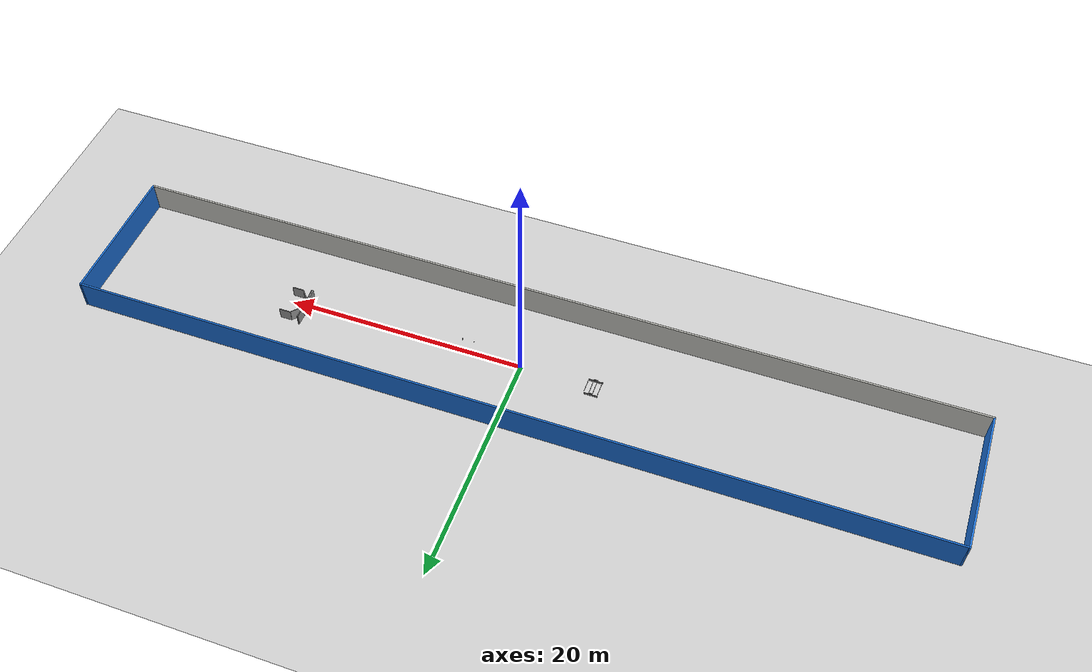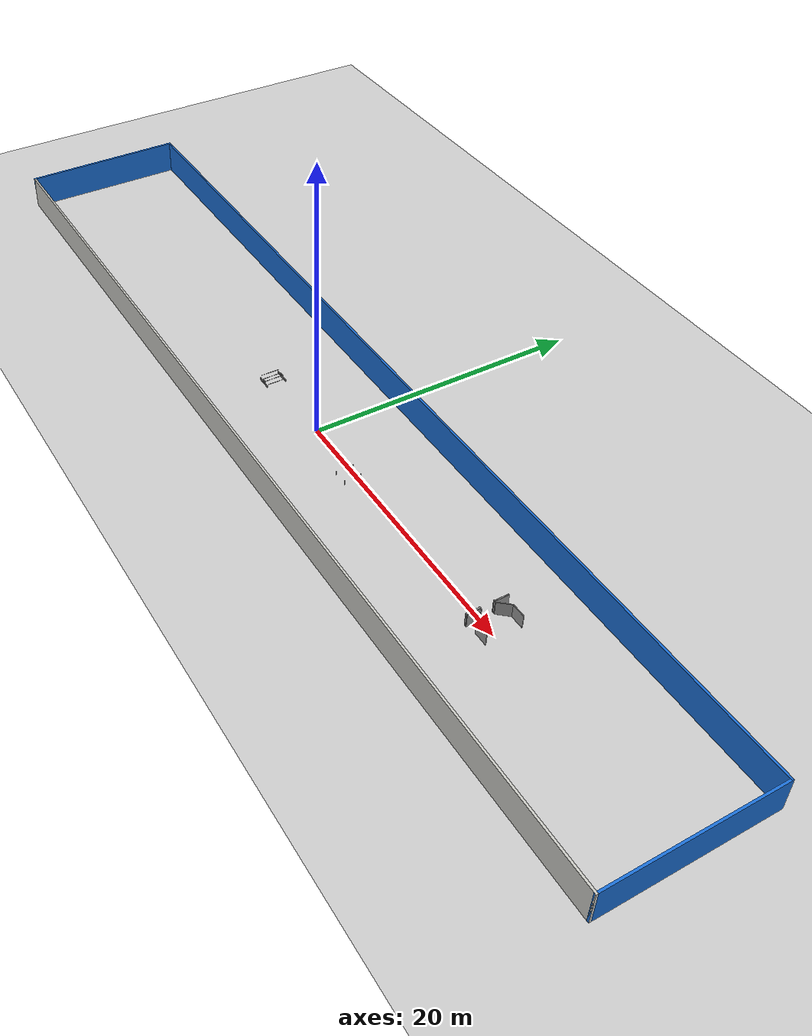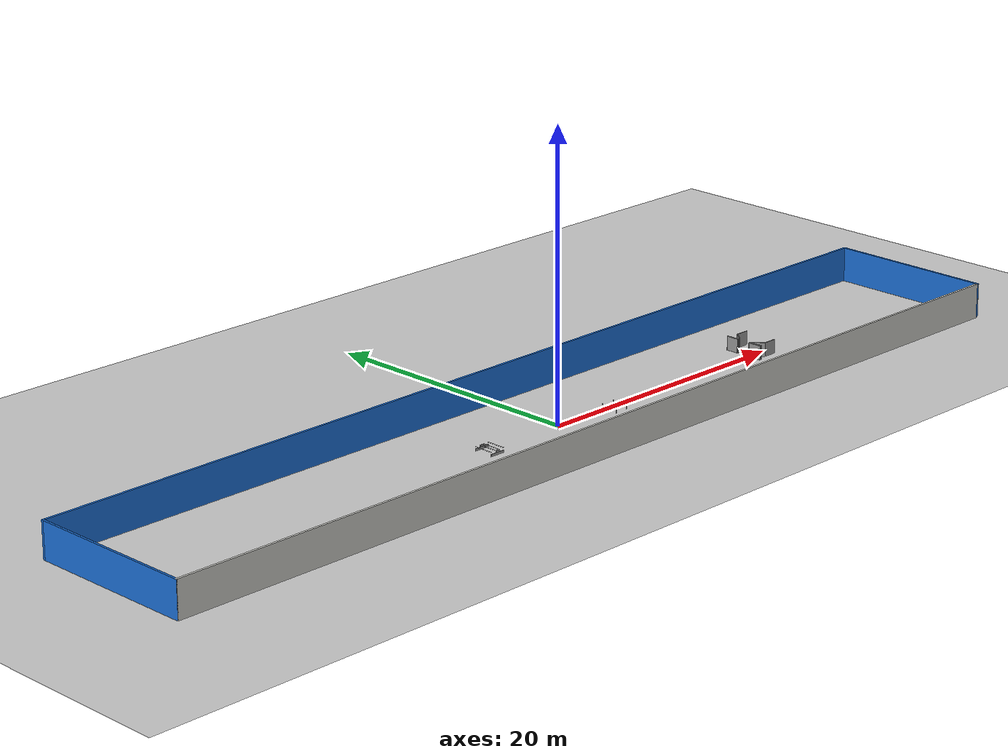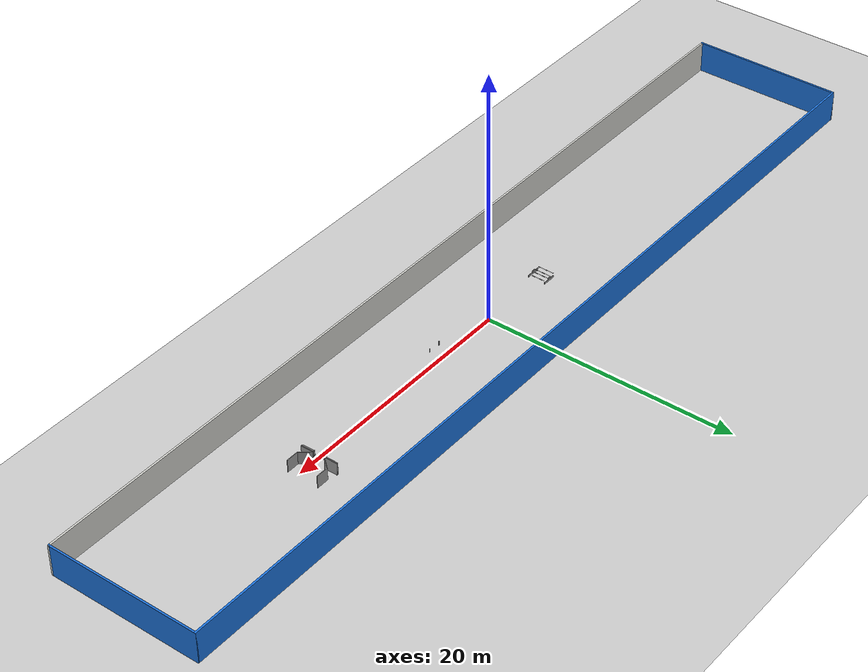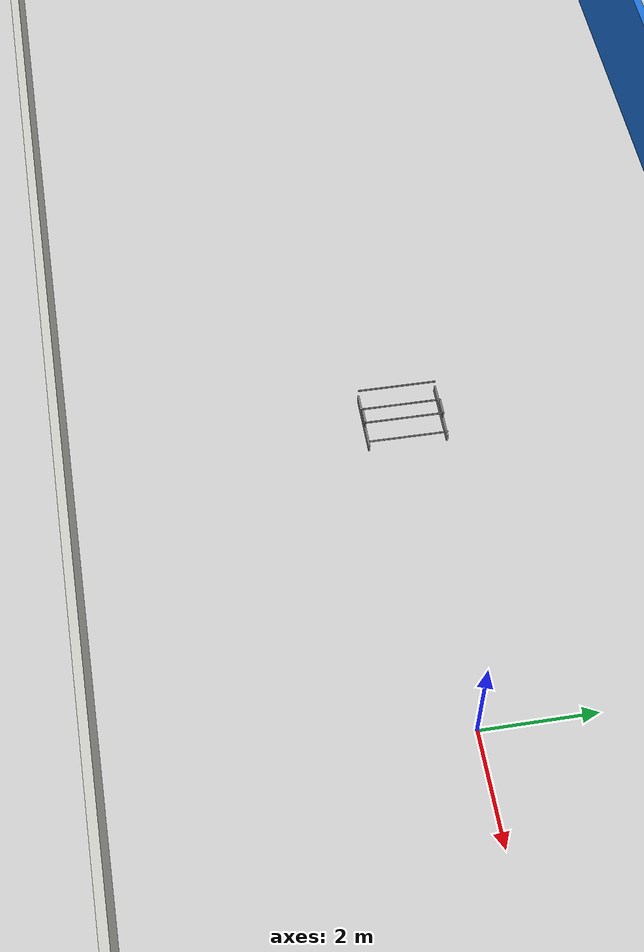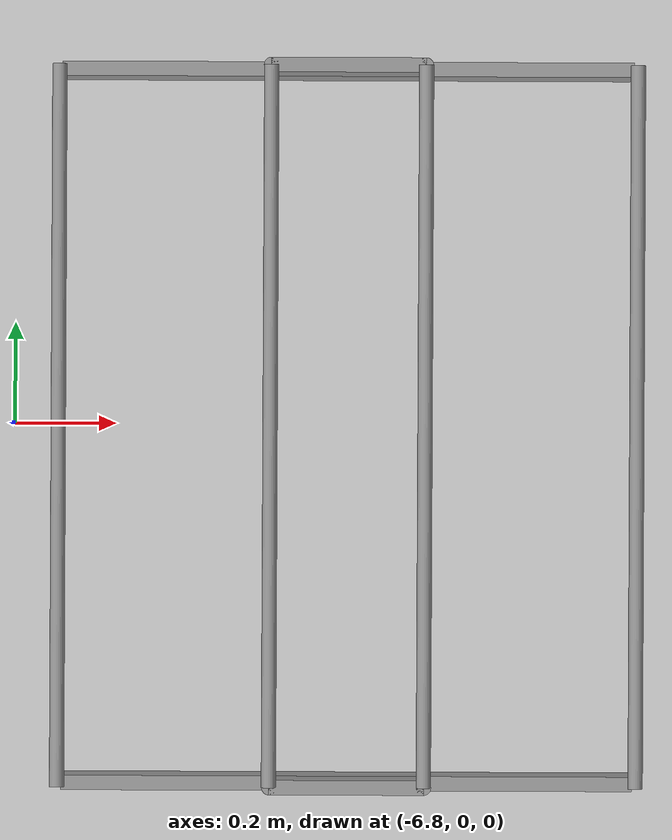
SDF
<sdf version="1.7">
 <world name="default">
  <light name="sun" type="directional">
   <pose>0 0 10 0 -0 0</pose>
   <diffuse>0.8 0.8 0.8 1</diffuse>
   <specular>0.2 0.2 0.2 1</specular>
   <attenuation>
    <range>1000</range>
    <constant>0.9</constant>
    <linear>0.01</linear>
    <quadratic>0.001</quadratic>
   </attenuation>
   <direction>-0.5 0.1 -0.9</direction>
   <spot><inner_angle>0</inner_angle><outer_angle>0</outer_angle><falloff>0</falloff></spot>
  </light>
  <model name="ground_plane">
   <static>1</static>
   <link name="link">
    <collision name="collision">
     <geometry><plane><normal>0 0 1</normal><size>100 100</size></plane></geometry>
     <surface>
      <contact><collide_bitmask>65535</collide_bitmask></contact>
      <friction><ode><mu>100</mu><mu2>50</mu2></ode></friction>
     </surface>
    </collision>
    <visual name="visual">
     <cast_shadows>0</cast_shadows>
     <geometry><plane><normal>0 0 1</normal><size>100 100</size></plane></geometry>
     <material>
      <script><uri>file://media/materials/scripts/gazebo.material</uri><name>Gazebo/Grey</name></script>
     </material>
    </visual>
   </link>
  </model>
  <gravity>0 0 -9.8</gravity>
  <magnetic_field>6e-06 2.3e-05 -4.2e-05</magnetic_field>
  <atmosphere type="adiabatic"/>
  <physics type="ode">
   <max_step_size>0.001</max_step_size>
   <real_time_factor>1</real_time_factor>
   <real_time_update_rate>1000</real_time_update_rate>
  </physics>
  <scene><ambient>0.4 0.4 0.4 1</ambient><background>0.7 0.7 0.7 1</background><shadows>1</shadows></scene>
  <audio><device>default</device></audio>
  <spherical_coordinates>
   <surface_model>EARTH_WGS84</surface_model>
   <latitude_deg>0</latitude_deg>
   <longitude_deg>0</longitude_deg>
   <elevation>0</elevation>
   <heading_deg>0</heading_deg>
  </spherical_coordinates>
  <model name="Marunda2">
   <link name="Wall_0">
    <collision name="Wall_0_Collision">
     <geometry><box><size>72.15 0.15 2.5</size></box></geometry>
     <pose>0 0 1.25 0 -0 0</pose>
    </collision>
    <visual name="Wall_0_Visual">
     <pose>0 0 1.25 0 -0 0</pose>
     <geometry><box><size>72.15 0.15 2.5</size></box></geometry>
     <material>
      <script><uri>file://media/materials/scripts/gazebo.material</uri><name>Gazebo/Grey</name></script>
      <ambient>0.109804 0.443137 0.847059 1</ambient>
     </material>
     <meta><layer>0</layer></meta>
    </visual>
    <pose>0 6 0 0 -0 0</pose>
   </link>
   <link name="Wall_2">
    <collision name="Wall_2_Collision">
     <geometry><box><size>72.15 0.15 2.5</size></box></geometry>
     <pose>0 0 1.25 0 -0 0</pose>
    </collision>
    <visual name="Wall_2_Visual">
     <pose>0 0 1.25 0 -0 0</pose>
     <geometry><box><size>72.15 0.15 2.5</size></box></geometry>
     <material>
      <script><uri>file://media/materials/scripts/gazebo.material</uri><name>Gazebo/CeilingTiled</name></script>
      <ambient>0.109804 0.443137 0.847059 1</ambient>
     </material>
     <meta><layer>0</layer></meta>
    </visual>
    <pose>0 -6 0 0 -0 0</pose>
   </link>
   <link name="Wall_4">
    <collision name="Wall_4_Collision">
     <geometry><box><size>12.15 0.15 2.5</size></box></geometry>
     <pose>0 0 1.25 0 -0 0</pose>
    </collision>
    <visual name="Wall_4_Visual">
     <pose>0 0 1.25 0 -0 0</pose>
     <geometry><box><size>12.15 0.15 2.5</size></box></geometry>
     <material>
      <script><uri>file://media/materials/scripts/gazebo.material</uri><name>Gazebo/Grey</name></script>
      <ambient>0.109804 0.443137 0.847059 1</ambient>
     </material>
     <meta><layer>0</layer></meta>
    </visual>
    <pose>-36 0 0 0 -0 -1.5708</pose>
   </link>
   <link name="Wall_6">
    <collision name="Wall_6_Collision">
     <geometry><box><size>12.15 0.15 2.5</size></box></geometry>
     <pose>0 0 1.25 0 -0 0</pose>
    </collision>
    <visual name="Wall_6_Visual">
     <pose>0 0 1.25 0 -0 0</pose>
     <geometry><box><size>12.15 0.15 2.5</size></box></geometry>
     <material>
      <script><uri>file://media/materials/scripts/gazebo.material</uri><name>Gazebo/Grey</name></script>
      <ambient>0.109804 0.443137 0.847059 1</ambient>
     </material>
     <meta><layer>0</layer></meta>
    </visual>
    <pose>36 0 0 0 -0 -1.5708</pose>
   </link>
   <static>1</static>
  </model>
  <model name="trolley2">
   <link name="link_0">
    <inertial>
     <mass>1.79769e+308</mass>
     <inertia>
      <ixx>1.79769e+308</ixx>
      <ixy>0</ixy>
      <ixz>0</ixz>
      <iyy>1.79769e+308</iyy>
      <iyz>0</iyz>
      <izz>1.79769e+308</izz>
     </inertia>
    </inertial>
    <pose>-0.5 -0.6 -0 0 -0 0</pose>
    <visual name="visual">
     <geometry><box><size>0.04 0.04 0.35</size></box></geometry>
     <material>
      <lighting>1</lighting>
      <script><uri>file://media/materials/scripts/gazebo.material</uri><name>Gazebo/Grey</name></script>
      <shader type="pixel"><normal_map>__default__</normal_map></shader>
      <ambient>0.3 0.3 0.3 1</ambient>
      <diffuse>0.7 0.7 0.7 1</diffuse>
      <specular>0.01 0.01 0.01 1</specular>
      <emissive>0 0 0 1</emissive>
     </material>
    </visual>
    <collision name="collision">
     <geometry><box><size>0.04 0.04 0.35</size></box></geometry>
     <surface>
      <friction>
       <ode><mu>1</mu><mu2>1</mu2><fdir1>0 0 0</fdir1><slip1>0</slip1><slip2>0</slip2></ode>
       <torsional>
        <coefficient>1</coefficient>
        <patch_radius>0</patch_radius>
        <surface_radius>0</surface_radius>
        <use_patch_radius>1</use_patch_radius>
        <ode><slip>0</slip></ode>
       </torsional>
      </friction>
      <bounce><restitution_coefficient>0</restitution_coefficient><threshold>1e+06</threshold></bounce>
      <contact>
       <collide_without_contact>0</collide_without_contact>
       <collide_without_contact_bitmask>1</collide_without_contact_bitmask>
       <collide_bitmask>1</collide_bitmask>
       <ode>
        <soft_cfm>0</soft_cfm>
        <soft_erp>0.2</soft_erp>
        <kp>1e+13</kp>
        <kd>1</kd>
        <max_vel>0.01</max_vel>
        <min_depth>0</min_depth>
       </ode>
       <bullet>
        <split_impulse>1</split_impulse>
        <split_impulse_penetration_threshold>-0.01</split_impulse_penetration_threshold>
        <soft_cfm>0</soft_cfm>
        <soft_erp>0.2</soft_erp>
        <kp>1e+13</kp>
        <kd>1</kd>
       </bullet>
      </contact>
     </surface>
    </collision>
    <collision name="collision_5">
     <geometry><box><size>0.04 0.04 0.35</size></box></geometry>
     <surface>
      <friction>
       <ode><mu>1</mu><mu2>1</mu2><fdir1>0 0 0</fdir1><slip1>0</slip1><slip2>0</slip2></ode>
       <torsional>
        <coefficient>1</coefficient>
        <patch_radius>0</patch_radius>
        <surface_radius>0</surface_radius>
        <use_patch_radius>1</use_patch_radius>
        <ode><slip>0</slip></ode>
       </torsional>
      </friction>
      <bounce><restitution_coefficient>0</restitution_coefficient><threshold>1e+06</threshold></bounce>
      <contact>
       <collide_without_contact>0</collide_without_contact>
       <collide_without_contact_bitmask>1</collide_without_contact_bitmask>
       <collide_bitmask>1</collide_bitmask>
       <ode>
        <soft_cfm>0</soft_cfm>
        <soft_erp>0.2</soft_erp>
        <kp>1e+13</kp>
        <kd>1</kd>
        <max_vel>0.01</max_vel>
        <min_depth>0</min_depth>
       </ode>
       <bullet>
        <split_impulse>1</split_impulse>
        <split_impulse_penetration_threshold>-0.01</split_impulse_penetration_threshold>
        <soft_cfm>0</soft_cfm>
        <soft_erp>0.2</soft_erp>
        <kp>1e+13</kp>
        <kd>1</kd>
       </bullet>
      </contact>
     </surface>
    </collision>
    <collision name="collision_1">
     <geometry><box><size>0.04 0.04 0.35</size></box></geometry>
     <surface>
      <friction>
       <ode><mu>1</mu><mu2>1</mu2><fdir1>0 0 0</fdir1><slip1>0</slip1><slip2>0</slip2></ode>
       <torsional>
        <coefficient>1</coefficient>
        <patch_radius>0</patch_radius>
        <surface_radius>0</surface_radius>
        <use_patch_radius>1</use_patch_radius>
        <ode><slip>0</slip></ode>
       </torsional>
      </friction>
      <bounce><restitution_coefficient>0</restitution_coefficient><threshold>1e+06</threshold></bounce>
      <contact>
       <collide_without_contact>0</collide_without_contact>
       <collide_without_contact_bitmask>1</collide_without_contact_bitmask>
       <collide_bitmask>1</collide_bitmask>
       <ode>
        <soft_cfm>0</soft_cfm>
        <soft_erp>0.2</soft_erp>
        <kp>1e+13</kp>
        <kd>1</kd>
        <max_vel>0.01</max_vel>
        <min_depth>0</min_depth>
       </ode>
       <bullet>
        <split_impulse>1</split_impulse>
        <split_impulse_penetration_threshold>-0.01</split_impulse_penetration_threshold>
        <soft_cfm>0</soft_cfm>
        <soft_erp>0.2</soft_erp>
        <kp>1e+13</kp>
        <kd>1</kd>
       </bullet>
      </contact>
     </surface>
    </collision>
    <collision name="collision_2">
     <geometry><box><size>0.04 0.04 0.35</size></box></geometry>
     <surface>
      <friction>
       <ode><mu>1</mu><mu2>1</mu2><fdir1>0 0 0</fdir1><slip1>0</slip1><slip2>0</slip2></ode>
       <torsional>
        <coefficient>1</coefficient>
        <patch_radius>0</patch_radius>
        <surface_radius>0</surface_radius>
        <use_patch_radius>1</use_patch_radius>
        <ode><slip>0</slip></ode>
       </torsional>
      </friction>
      <bounce><restitution_coefficient>0</restitution_coefficient><threshold>1e+06</threshold></bounce>
      <contact>
       <collide_without_contact>0</collide_without_contact>
       <collide_without_contact_bitmask>1</collide_without_contact_bitmask>
       <collide_bitmask>1</collide_bitmask>
       <ode>
        <soft_cfm>0</soft_cfm>
        <soft_erp>0.2</soft_erp>
        <kp>1e+13</kp>
        <kd>1</kd>
        <max_vel>0.01</max_vel>
        <min_depth>0</min_depth>
       </ode>
       <bullet>
        <split_impulse>1</split_impulse>
        <split_impulse_penetration_threshold>-0.01</split_impulse_penetration_threshold>
        <soft_cfm>0</soft_cfm>
        <soft_erp>0.2</soft_erp>
        <kp>1e+13</kp>
        <kd>1</kd>
       </bullet>
      </contact>
     </surface>
    </collision>
    <collision name="collision_3">
     <geometry><box><size>0.04 0.04 0.35</size></box></geometry>
     <surface>
      <friction>
       <ode><mu>1</mu><mu2>1</mu2><fdir1>0 0 0</fdir1><slip1>0</slip1><slip2>0</slip2></ode>
       <torsional>
        <coefficient>1</coefficient>
        <patch_radius>0</patch_radius>
        <surface_radius>0</surface_radius>
        <use_patch_radius>1</use_patch_radius>
        <ode><slip>0</slip></ode>
       </torsional>
      </friction>
      <bounce><restitution_coefficient>0</restitution_coefficient><threshold>1e+06</threshold></bounce>
      <contact>
       <collide_without_contact>0</collide_without_contact>
       <collide_without_contact_bitmask>1</collide_without_contact_bitmask>
       <collide_bitmask>1</collide_bitmask>
       <ode>
        <soft_cfm>0</soft_cfm>
        <soft_erp>0.2</soft_erp>
        <kp>1e+13</kp>
        <kd>1</kd>
        <max_vel>0.01</max_vel>
        <min_depth>0</min_depth>
       </ode>
       <bullet>
        <split_impulse>1</split_impulse>
        <split_impulse_penetration_threshold>-0.01</split_impulse_penetration_threshold>
        <soft_cfm>0</soft_cfm>
        <soft_erp>0.2</soft_erp>
        <kp>1e+13</kp>
        <kd>1</kd>
       </bullet>
      </contact>
     </surface>
    </collision>
    <collision name="collision_4">
     <geometry><sphere><radius>1.79769e+308</radius></sphere></geometry>
     <surface>
      <friction>
       <ode><mu>1</mu><mu2>1</mu2><fdir1>0 0 0</fdir1><slip1>0</slip1><slip2>0</slip2></ode>
       <torsional>
        <coefficient>1</coefficient>
        <patch_radius>0</patch_radius>
        <surface_radius>0</surface_radius>
        <use_patch_radius>1</use_patch_radius>
        <ode><slip>0</slip></ode>
       </torsional>
      </friction>
      <bounce><restitution_coefficient>0</restitution_coefficient><threshold>1e+06</threshold></bounce>
      <contact>
       <collide_without_contact>0</collide_without_contact>
       <collide_without_contact_bitmask>1</collide_without_contact_bitmask>
       <collide_bitmask>1</collide_bitmask>
       <ode>
        <soft_cfm>0</soft_cfm>
        <soft_erp>0.2</soft_erp>
        <kp>1e+13</kp>
        <kd>1</kd>
        <max_vel>0.01</max_vel>
        <min_depth>0</min_depth>
       </ode>
       <bullet>
        <split_impulse>1</split_impulse>
        <split_impulse_penetration_threshold>-0.01</split_impulse_penetration_threshold>
        <soft_cfm>0</soft_cfm>
        <soft_erp>0.2</soft_erp>
        <kp>1e+13</kp>
        <kd>1</kd>
       </bullet>
      </contact>
     </surface>
    </collision>
   </link>
   <link name="link_0_clone">
    <inertial>
     <mass>1.79769e+308</mass>
     <inertia>
      <ixx>1.79769e+308</ixx>
      <ixy>0</ixy>
      <ixz>0</ixz>
      <iyy>1.79769e+308</iyy>
      <iyz>0</iyz>
      <izz>1.79769e+308</izz>
     </inertia>
    </inertial>
    <pose>-0.5 0.6 -0 0 -0 0</pose>
    <visual name="visual">
     <geometry><box><size>0.04 0.04 0.35</size></box></geometry>
     <material>
      <lighting>1</lighting>
      <script><uri>file://media/materials/scripts/gazebo.material</uri><name>Gazebo/Grey</name></script>
      <shader type="pixel"><normal_map>__default__</normal_map></shader>
      <ambient>0.3 0.3 0.3 1</ambient>
      <diffuse>0.7 0.7 0.7 1</diffuse>
      <specular>0.01 0.01 0.01 1</specular>
      <emissive>0 0 0 1</emissive>
     </material>
    </visual>
    <collision name="collision">
     <geometry><box><size>0.04 0.04 0.35</size></box></geometry>
     <surface>
      <friction>
       <ode><mu>1</mu><mu2>1</mu2><fdir1>0 0 0</fdir1><slip1>0</slip1><slip2>0</slip2></ode>
       <torsional>
        <coefficient>1</coefficient>
        <patch_radius>0</patch_radius>
        <surface_radius>0</surface_radius>
        <use_patch_radius>1</use_patch_radius>
        <ode><slip>0</slip></ode>
       </torsional>
      </friction>
      <bounce><restitution_coefficient>0</restitution_coefficient><threshold>1e+06</threshold></bounce>
      <contact>
       <collide_without_contact>0</collide_without_contact>
       <collide_without_contact_bitmask>1</collide_without_contact_bitmask>
       <collide_bitmask>1</collide_bitmask>
       <ode>
        <soft_cfm>0</soft_cfm>
        <soft_erp>0.2</soft_erp>
        <kp>1e+13</kp>
        <kd>1</kd>
        <max_vel>0.01</max_vel>
        <min_depth>0</min_depth>
       </ode>
       <bullet>
        <split_impulse>1</split_impulse>
        <split_impulse_penetration_threshold>-0.01</split_impulse_penetration_threshold>
        <soft_cfm>0</soft_cfm>
        <soft_erp>0.2</soft_erp>
        <kp>1e+13</kp>
        <kd>1</kd>
       </bullet>
      </contact>
     </surface>
    </collision>
    <collision name="collision_5">
     <geometry><box><size>0.04 0.04 0.35</size></box></geometry>
     <surface>
      <friction>
       <ode><mu>1</mu><mu2>1</mu2><fdir1>0 0 0</fdir1><slip1>0</slip1><slip2>0</slip2></ode>
       <torsional>
        <coefficient>1</coefficient>
        <patch_radius>0</patch_radius>
        <surface_radius>0</surface_radius>
        <use_patch_radius>1</use_patch_radius>
        <ode><slip>0</slip></ode>
       </torsional>
      </friction>
      <bounce><restitution_coefficient>0</restitution_coefficient><threshold>1e+06</threshold></bounce>
      <contact>
       <collide_without_contact>0</collide_without_contact>
       <collide_without_contact_bitmask>1</collide_without_contact_bitmask>
       <collide_bitmask>1</collide_bitmask>
       <ode>
        <soft_cfm>0</soft_cfm>
        <soft_erp>0.2</soft_erp>
        <kp>1e+13</kp>
        <kd>1</kd>
        <max_vel>0.01</max_vel>
        <min_depth>0</min_depth>
       </ode>
       <bullet>
        <split_impulse>1</split_impulse>
        <split_impulse_penetration_threshold>-0.01</split_impulse_penetration_threshold>
        <soft_cfm>0</soft_cfm>
        <soft_erp>0.2</soft_erp>
        <kp>1e+13</kp>
        <kd>1</kd>
       </bullet>
      </contact>
     </surface>
    </collision>
    <collision name="collision_1">
     <geometry><box><size>0.04 0.04 0.35</size></box></geometry>
     <surface>
      <friction>
       <ode><mu>1</mu><mu2>1</mu2><fdir1>0 0 0</fdir1><slip1>0</slip1><slip2>0</slip2></ode>
       <torsional>
        <coefficient>1</coefficient>
        <patch_radius>0</patch_radius>
        <surface_radius>0</surface_radius>
        <use_patch_radius>1</use_patch_radius>
        <ode><slip>0</slip></ode>
       </torsional>
      </friction>
      <bounce><restitution_coefficient>0</restitution_coefficient><threshold>1e+06</threshold></bounce>
      <contact>
       <collide_without_contact>0</collide_without_contact>
       <collide_without_contact_bitmask>1</collide_without_contact_bitmask>
       <collide_bitmask>1</collide_bitmask>
       <ode>
        <soft_cfm>0</soft_cfm>
        <soft_erp>0.2</soft_erp>
        <kp>1e+13</kp>
        <kd>1</kd>
        <max_vel>0.01</max_vel>
        <min_depth>0</min_depth>
       </ode>
       <bullet>
        <split_impulse>1</split_impulse>
        <split_impulse_penetration_threshold>-0.01</split_impulse_penetration_threshold>
        <soft_cfm>0</soft_cfm>
        <soft_erp>0.2</soft_erp>
        <kp>1e+13</kp>
        <kd>1</kd>
       </bullet>
      </contact>
     </surface>
    </collision>
    <collision name="collision_2">
     <geometry><box><size>0.04 0.04 0.35</size></box></geometry>
     <surface>
      <friction>
       <ode><mu>1</mu><mu2>1</mu2><fdir1>0 0 0</fdir1><slip1>0</slip1><slip2>0</slip2></ode>
       <torsional>
        <coefficient>1</coefficient>
        <patch_radius>0</patch_radius>
        <surface_radius>0</surface_radius>
        <use_patch_radius>1</use_patch_radius>
        <ode><slip>0</slip></ode>
       </torsional>
      </friction>
      <bounce><restitution_coefficient>0</restitution_coefficient><threshold>1e+06</threshold></bounce>
      <contact>
       <collide_without_contact>0</collide_without_contact>
       <collide_without_contact_bitmask>1</collide_without_contact_bitmask>
       <collide_bitmask>1</collide_bitmask>
       <ode>
        <soft_cfm>0</soft_cfm>
        <soft_erp>0.2</soft_erp>
        <kp>1e+13</kp>
        <kd>1</kd>
        <max_vel>0.01</max_vel>
        <min_depth>0</min_depth>
       </ode>
       <bullet>
        <split_impulse>1</split_impulse>
        <split_impulse_penetration_threshold>-0.01</split_impulse_penetration_threshold>
        <soft_cfm>0</soft_cfm>
        <soft_erp>0.2</soft_erp>
        <kp>1e+13</kp>
        <kd>1</kd>
       </bullet>
      </contact>
     </surface>
    </collision>
    <collision name="collision_3">
     <geometry><box><size>0.04 0.04 0.35</size></box></geometry>
     <surface>
      <friction>
       <ode><mu>1</mu><mu2>1</mu2><fdir1>0 0 0</fdir1><slip1>0</slip1><slip2>0</slip2></ode>
       <torsional>
        <coefficient>1</coefficient>
        <patch_radius>0</patch_radius>
        <surface_radius>0</surface_radius>
        <use_patch_radius>1</use_patch_radius>
        <ode><slip>0</slip></ode>
       </torsional>
      </friction>
      <bounce><restitution_coefficient>0</restitution_coefficient><threshold>1e+06</threshold></bounce>
      <contact>
       <collide_without_contact>0</collide_without_contact>
       <collide_without_contact_bitmask>1</collide_without_contact_bitmask>
       <collide_bitmask>1</collide_bitmask>
       <ode>
        <soft_cfm>0</soft_cfm>
        <soft_erp>0.2</soft_erp>
        <kp>1e+13</kp>
        <kd>1</kd>
        <max_vel>0.01</max_vel>
        <min_depth>0</min_depth>
       </ode>
       <bullet>
        <split_impulse>1</split_impulse>
        <split_impulse_penetration_threshold>-0.01</split_impulse_penetration_threshold>
        <soft_cfm>0</soft_cfm>
        <soft_erp>0.2</soft_erp>
        <kp>1e+13</kp>
        <kd>1</kd>
       </bullet>
      </contact>
     </surface>
    </collision>
    <collision name="collision_4">
     <geometry><sphere><radius>1.79769e+308</radius></sphere></geometry>
     <surface>
      <friction>
       <ode><mu>1</mu><mu2>1</mu2><fdir1>0 0 0</fdir1><slip1>0</slip1><slip2>0</slip2></ode>
       <torsional>
        <coefficient>1</coefficient>
        <patch_radius>0</patch_radius>
        <surface_radius>0</surface_radius>
        <use_patch_radius>1</use_patch_radius>
        <ode><slip>0</slip></ode>
       </torsional>
      </friction>
      <bounce><restitution_coefficient>0</restitution_coefficient><threshold>1e+06</threshold></bounce>
      <contact>
       <collide_without_contact>0</collide_without_contact>
       <collide_without_contact_bitmask>1</collide_without_contact_bitmask>
       <collide_bitmask>1</collide_bitmask>
       <ode>
        <soft_cfm>0</soft_cfm>
        <soft_erp>0.2</soft_erp>
        <kp>1e+13</kp>
        <kd>1</kd>
        <max_vel>0.01</max_vel>
        <min_depth>0</min_depth>
       </ode>
       <bullet>
        <split_impulse>1</split_impulse>
        <split_impulse_penetration_threshold>-0.01</split_impulse_penetration_threshold>
        <soft_cfm>0</soft_cfm>
        <soft_erp>0.2</soft_erp>
        <kp>1e+13</kp>
        <kd>1</kd>
       </bullet>
      </contact>
     </surface>
    </collision>
   </link>
   <link name="link_0_clone_clone">
    <inertial>
     <mass>1.79769e+308</mass>
     <inertia>
      <ixx>1.79769e+308</ixx>
      <ixy>0</ixy>
      <ixz>0</ixz>
      <iyy>1.79769e+308</iyy>
      <iyz>0</iyz>
      <izz>1.79769e+308</izz>
     </inertia>
    </inertial>
    <pose>0.5 0.6 -0 0 -0 0</pose>
    <visual name="visual">
     <geometry><box><size>0.04 0.04 0.35</size></box></geometry>
     <material>
      <lighting>1</lighting>
      <script><uri>file://media/materials/scripts/gazebo.material</uri><name>Gazebo/Grey</name></script>
      <shader type="pixel"><normal_map>__default__</normal_map></shader>
      <ambient>0.3 0.3 0.3 1</ambient>
      <diffuse>0.7 0.7 0.7 1</diffuse>
      <specular>0.01 0.01 0.01 1</specular>
      <emissive>0 0 0 1</emissive>
     </material>
    </visual>
    <collision name="collision">
     <geometry><box><size>0.04 0.04 0.35</size></box></geometry>
     <surface>
      <friction>
       <ode><mu>1</mu><mu2>1</mu2><fdir1>0 0 0</fdir1><slip1>0</slip1><slip2>0</slip2></ode>
       <torsional>
        <coefficient>1</coefficient>
        <patch_radius>0</patch_radius>
        <surface_radius>0</surface_radius>
        <use_patch_radius>1</use_patch_radius>
        <ode><slip>0</slip></ode>
       </torsional>
      </friction>
      <bounce><restitution_coefficient>0</restitution_coefficient><threshold>1e+06</threshold></bounce>
      <contact>
       <collide_without_contact>0</collide_without_contact>
       <collide_without_contact_bitmask>1</collide_without_contact_bitmask>
       <collide_bitmask>1</collide_bitmask>
       <ode>
        <soft_cfm>0</soft_cfm>
        <soft_erp>0.2</soft_erp>
        <kp>1e+13</kp>
        <kd>1</kd>
        <max_vel>0.01</max_vel>
        <min_depth>0</min_depth>
       </ode>
       <bullet>
        <split_impulse>1</split_impulse>
        <split_impulse_penetration_threshold>-0.01</split_impulse_penetration_threshold>
        <soft_cfm>0</soft_cfm>
        <soft_erp>0.2</soft_erp>
        <kp>1e+13</kp>
        <kd>1</kd>
       </bullet>
      </contact>
     </surface>
    </collision>
    <collision name="collision_1">
     <geometry><box><size>0.04 0.04 0.35</size></box></geometry>
     <surface>
      <friction>
       <ode><mu>1</mu><mu2>1</mu2><fdir1>0 0 0</fdir1><slip1>0</slip1><slip2>0</slip2></ode>
       <torsional>
        <coefficient>1</coefficient>
        <patch_radius>0</patch_radius>
        <surface_radius>0</surface_radius>
        <use_patch_radius>1</use_patch_radius>
        <ode><slip>0</slip></ode>
       </torsional>
      </friction>
      <bounce><restitution_coefficient>0</restitution_coefficient><threshold>1e+06</threshold></bounce>
      <contact>
       <collide_without_contact>0</collide_without_contact>
       <collide_without_contact_bitmask>1</collide_without_contact_bitmask>
       <collide_bitmask>1</collide_bitmask>
       <ode>
        <soft_cfm>0</soft_cfm>
        <soft_erp>0.2</soft_erp>
        <kp>1e+13</kp>
        <kd>1</kd>
        <max_vel>0.01</max_vel>
        <min_depth>0</min_depth>
       </ode>
       <bullet>
        <split_impulse>1</split_impulse>
        <split_impulse_penetration_threshold>-0.01</split_impulse_penetration_threshold>
        <soft_cfm>0</soft_cfm>
        <soft_erp>0.2</soft_erp>
        <kp>1e+13</kp>
        <kd>1</kd>
       </bullet>
      </contact>
     </surface>
    </collision>
    <collision name="collision_5">
     <geometry><box><size>0.04 0.04 0.35</size></box></geometry>
     <surface>
      <friction>
       <ode><mu>1</mu><mu2>1</mu2><fdir1>0 0 0</fdir1><slip1>0</slip1><slip2>0</slip2></ode>
       <torsional>
        <coefficient>1</coefficient>
        <patch_radius>0</patch_radius>
        <surface_radius>0</surface_radius>
        <use_patch_radius>1</use_patch_radius>
        <ode><slip>0</slip></ode>
       </torsional>
      </friction>
      <bounce><restitution_coefficient>0</restitution_coefficient><threshold>1e+06</threshold></bounce>
      <contact>
       <collide_without_contact>0</collide_without_contact>
       <collide_without_contact_bitmask>1</collide_without_contact_bitmask>
       <collide_bitmask>1</collide_bitmask>
       <ode>
        <soft_cfm>0</soft_cfm>
        <soft_erp>0.2</soft_erp>
        <kp>1e+13</kp>
        <kd>1</kd>
        <max_vel>0.01</max_vel>
        <min_depth>0</min_depth>
       </ode>
       <bullet>
        <split_impulse>1</split_impulse>
        <split_impulse_penetration_threshold>-0.01</split_impulse_penetration_threshold>
        <soft_cfm>0</soft_cfm>
        <soft_erp>0.2</soft_erp>
        <kp>1e+13</kp>
        <kd>1</kd>
       </bullet>
      </contact>
     </surface>
    </collision>
    <collision name="collision_2">
     <geometry><box><size>0.04 0.04 0.35</size></box></geometry>
     <surface>
      <friction>
       <ode><mu>1</mu><mu2>1</mu2><fdir1>0 0 0</fdir1><slip1>0</slip1><slip2>0</slip2></ode>
       <torsional>
        <coefficient>1</coefficient>
        <patch_radius>0</patch_radius>
        <surface_radius>0</surface_radius>
        <use_patch_radius>1</use_patch_radius>
        <ode><slip>0</slip></ode>
       </torsional>
      </friction>
      <bounce><restitution_coefficient>0</restitution_coefficient><threshold>1e+06</threshold></bounce>
      <contact>
       <collide_without_contact>0</collide_without_contact>
       <collide_without_contact_bitmask>1</collide_without_contact_bitmask>
       <collide_bitmask>1</collide_bitmask>
       <ode>
        <soft_cfm>0</soft_cfm>
        <soft_erp>0.2</soft_erp>
        <kp>1e+13</kp>
        <kd>1</kd>
        <max_vel>0.01</max_vel>
        <min_depth>0</min_depth>
       </ode>
       <bullet>
        <split_impulse>1</split_impulse>
        <split_impulse_penetration_threshold>-0.01</split_impulse_penetration_threshold>
        <soft_cfm>0</soft_cfm>
        <soft_erp>0.2</soft_erp>
        <kp>1e+13</kp>
        <kd>1</kd>
       </bullet>
      </contact>
     </surface>
    </collision>
    <collision name="collision_3">
     <geometry><box><size>0.04 0.04 0.35</size></box></geometry>
     <surface>
      <friction>
       <ode><mu>1</mu><mu2>1</mu2><fdir1>0 0 0</fdir1><slip1>0</slip1><slip2>0</slip2></ode>
       <torsional>
        <coefficient>1</coefficient>
        <patch_radius>0</patch_radius>
        <surface_radius>0</surface_radius>
        <use_patch_radius>1</use_patch_radius>
        <ode><slip>0</slip></ode>
       </torsional>
      </friction>
      <bounce><restitution_coefficient>0</restitution_coefficient><threshold>1e+06</threshold></bounce>
      <contact>
       <collide_without_contact>0</collide_without_contact>
       <collide_without_contact_bitmask>1</collide_without_contact_bitmask>
       <collide_bitmask>1</collide_bitmask>
       <ode>
        <soft_cfm>0</soft_cfm>
        <soft_erp>0.2</soft_erp>
        <kp>1e+13</kp>
        <kd>1</kd>
        <max_vel>0.01</max_vel>
        <min_depth>0</min_depth>
       </ode>
       <bullet>
        <split_impulse>1</split_impulse>
        <split_impulse_penetration_threshold>-0.01</split_impulse_penetration_threshold>
        <soft_cfm>0</soft_cfm>
        <soft_erp>0.2</soft_erp>
        <kp>1e+13</kp>
        <kd>1</kd>
       </bullet>
      </contact>
     </surface>
    </collision>
    <collision name="collision_4">
     <geometry><sphere><radius>1.79769e+308</radius></sphere></geometry>
     <surface>
      <friction>
       <ode><mu>1</mu><mu2>1</mu2><fdir1>0 0 0</fdir1><slip1>0</slip1><slip2>0</slip2></ode>
       <torsional>
        <coefficient>1</coefficient>
        <patch_radius>0</patch_radius>
        <surface_radius>0</surface_radius>
        <use_patch_radius>1</use_patch_radius>
        <ode><slip>0</slip></ode>
       </torsional>
      </friction>
      <bounce><restitution_coefficient>0</restitution_coefficient><threshold>1e+06</threshold></bounce>
      <contact>
       <collide_without_contact>0</collide_without_contact>
       <collide_without_contact_bitmask>1</collide_without_contact_bitmask>
       <collide_bitmask>1</collide_bitmask>
       <ode>
        <soft_cfm>0</soft_cfm>
        <soft_erp>0.2</soft_erp>
        <kp>1e+13</kp>
        <kd>1</kd>
        <max_vel>0.01</max_vel>
        <min_depth>0</min_depth>
       </ode>
       <bullet>
        <split_impulse>1</split_impulse>
        <split_impulse_penetration_threshold>-0.01</split_impulse_penetration_threshold>
        <soft_cfm>0</soft_cfm>
        <soft_erp>0.2</soft_erp>
        <kp>1e+13</kp>
        <kd>1</kd>
       </bullet>
      </contact>
     </surface>
    </collision>
   </link>
   <link name="link_0_clone_clone_clone">
    <inertial>
     <mass>1.79769e+308</mass>
     <inertia>
      <ixx>1.79769e+308</ixx>
      <ixy>0</ixy>
      <ixz>0</ixz>
      <iyy>1.79769e+308</iyy>
      <iyz>0</iyz>
      <izz>1.79769e+308</izz>
     </inertia>
    </inertial>
    <pose>0.5 -0.6 -0 0 -0 0</pose>
    <visual name="visual">
     <geometry><box><size>0.04 0.04 0.35</size></box></geometry>
     <material>
      <lighting>1</lighting>
      <script><uri>file://media/materials/scripts/gazebo.material</uri><name>Gazebo/Grey</name></script>
      <shader type="pixel"><normal_map>__default__</normal_map></shader>
      <ambient>0.3 0.3 0.3 1</ambient>
      <diffuse>0.7 0.7 0.7 1</diffuse>
      <specular>0.01 0.01 0.01 1</specular>
      <emissive>0 0 0 1</emissive>
     </material>
    </visual>
    <collision name="collision">
     <geometry><box><size>0.04 0.04 0.35</size></box></geometry>
     <surface>
      <friction>
       <ode><mu>1</mu><mu2>1</mu2><fdir1>0 0 0</fdir1><slip1>0</slip1><slip2>0</slip2></ode>
       <torsional>
        <coefficient>1</coefficient>
        <patch_radius>0</patch_radius>
        <surface_radius>0</surface_radius>
        <use_patch_radius>1</use_patch_radius>
        <ode><slip>0</slip></ode>
       </torsional>
      </friction>
      <bounce><restitution_coefficient>0</restitution_coefficient><threshold>1e+06</threshold></bounce>
      <contact>
       <collide_without_contact>0</collide_without_contact>
       <collide_without_contact_bitmask>1</collide_without_contact_bitmask>
       <collide_bitmask>1</collide_bitmask>
       <ode>
        <soft_cfm>0</soft_cfm>
        <soft_erp>0.2</soft_erp>
        <kp>1e+13</kp>
        <kd>1</kd>
        <max_vel>0.01</max_vel>
        <min_depth>0</min_depth>
       </ode>
       <bullet>
        <split_impulse>1</split_impulse>
        <split_impulse_penetration_threshold>-0.01</split_impulse_penetration_threshold>
        <soft_cfm>0</soft_cfm>
        <soft_erp>0.2</soft_erp>
        <kp>1e+13</kp>
        <kd>1</kd>
       </bullet>
      </contact>
     </surface>
    </collision>
    <collision name="collision_5">
     <geometry><box><size>0.04 0.04 0.35</size></box></geometry>
     <surface>
      <friction>
       <ode><mu>1</mu><mu2>1</mu2><fdir1>0 0 0</fdir1><slip1>0</slip1><slip2>0</slip2></ode>
       <torsional>
        <coefficient>1</coefficient>
        <patch_radius>0</patch_radius>
        <surface_radius>0</surface_radius>
        <use_patch_radius>1</use_patch_radius>
        <ode><slip>0</slip></ode>
       </torsional>
      </friction>
      <bounce><restitution_coefficient>0</restitution_coefficient><threshold>1e+06</threshold></bounce>
      <contact>
       <collide_without_contact>0</collide_without_contact>
       <collide_without_contact_bitmask>1</collide_without_contact_bitmask>
       <collide_bitmask>1</collide_bitmask>
       <ode>
        <soft_cfm>0</soft_cfm>
        <soft_erp>0.2</soft_erp>
        <kp>1e+13</kp>
        <kd>1</kd>
        <max_vel>0.01</max_vel>
        <min_depth>0</min_depth>
       </ode>
       <bullet>
        <split_impulse>1</split_impulse>
        <split_impulse_penetration_threshold>-0.01</split_impulse_penetration_threshold>
        <soft_cfm>0</soft_cfm>
        <soft_erp>0.2</soft_erp>
        <kp>1e+13</kp>
        <kd>1</kd>
       </bullet>
      </contact>
     </surface>
    </collision>
    <collision name="collision_1">
     <geometry><box><size>0.04 0.04 0.35</size></box></geometry>
     <surface>
      <friction>
       <ode><mu>1</mu><mu2>1</mu2><fdir1>0 0 0</fdir1><slip1>0</slip1><slip2>0</slip2></ode>
       <torsional>
        <coefficient>1</coefficient>
        <patch_radius>0</patch_radius>
        <surface_radius>0</surface_radius>
        <use_patch_radius>1</use_patch_radius>
        <ode><slip>0</slip></ode>
       </torsional>
      </friction>
      <bounce><restitution_coefficient>0</restitution_coefficient><threshold>1e+06</threshold></bounce>
      <contact>
       <collide_without_contact>0</collide_without_contact>
       <collide_without_contact_bitmask>1</collide_without_contact_bitmask>
       <collide_bitmask>1</collide_bitmask>
       <ode>
        <soft_cfm>0</soft_cfm>
        <soft_erp>0.2</soft_erp>
        <kp>1e+13</kp>
        <kd>1</kd>
        <max_vel>0.01</max_vel>
        <min_depth>0</min_depth>
       </ode>
       <bullet>
        <split_impulse>1</split_impulse>
        <split_impulse_penetration_threshold>-0.01</split_impulse_penetration_threshold>
        <soft_cfm>0</soft_cfm>
        <soft_erp>0.2</soft_erp>
        <kp>1e+13</kp>
        <kd>1</kd>
       </bullet>
      </contact>
     </surface>
    </collision>
    <collision name="collision_2">
     <geometry><box><size>0.04 0.04 0.35</size></box></geometry>
     <surface>
      <friction>
       <ode><mu>1</mu><mu2>1</mu2><fdir1>0 0 0</fdir1><slip1>0</slip1><slip2>0</slip2></ode>
       <torsional>
        <coefficient>1</coefficient>
        <patch_radius>0</patch_radius>
        <surface_radius>0</surface_radius>
        <use_patch_radius>1</use_patch_radius>
        <ode><slip>0</slip></ode>
       </torsional>
      </friction>
      <bounce><restitution_coefficient>0</restitution_coefficient><threshold>1e+06</threshold></bounce>
      <contact>
       <collide_without_contact>0</collide_without_contact>
       <collide_without_contact_bitmask>1</collide_without_contact_bitmask>
       <collide_bitmask>1</collide_bitmask>
       <ode>
        <soft_cfm>0</soft_cfm>
        <soft_erp>0.2</soft_erp>
        <kp>1e+13</kp>
        <kd>1</kd>
        <max_vel>0.01</max_vel>
        <min_depth>0</min_depth>
       </ode>
       <bullet>
        <split_impulse>1</split_impulse>
        <split_impulse_penetration_threshold>-0.01</split_impulse_penetration_threshold>
        <soft_cfm>0</soft_cfm>
        <soft_erp>0.2</soft_erp>
        <kp>1e+13</kp>
        <kd>1</kd>
       </bullet>
      </contact>
     </surface>
    </collision>
    <collision name="collision_3">
     <geometry><box><size>0.04 0.04 0.35</size></box></geometry>
     <surface>
      <friction>
       <ode><mu>1</mu><mu2>1</mu2><fdir1>0 0 0</fdir1><slip1>0</slip1><slip2>0</slip2></ode>
       <torsional>
        <coefficient>1</coefficient>
        <patch_radius>0</patch_radius>
        <surface_radius>0</surface_radius>
        <use_patch_radius>1</use_patch_radius>
        <ode><slip>0</slip></ode>
       </torsional>
      </friction>
      <bounce><restitution_coefficient>0</restitution_coefficient><threshold>1e+06</threshold></bounce>
      <contact>
       <collide_without_contact>0</collide_without_contact>
       <collide_without_contact_bitmask>1</collide_without_contact_bitmask>
       <collide_bitmask>1</collide_bitmask>
       <ode>
        <soft_cfm>0</soft_cfm>
        <soft_erp>0.2</soft_erp>
        <kp>1e+13</kp>
        <kd>1</kd>
        <max_vel>0.01</max_vel>
        <min_depth>0</min_depth>
       </ode>
       <bullet>
        <split_impulse>1</split_impulse>
        <split_impulse_penetration_threshold>-0.01</split_impulse_penetration_threshold>
        <soft_cfm>0</soft_cfm>
        <soft_erp>0.2</soft_erp>
        <kp>1e+13</kp>
        <kd>1</kd>
       </bullet>
      </contact>
     </surface>
    </collision>
    <collision name="collision_4">
     <geometry><sphere><radius>1.79769e+308</radius></sphere></geometry>
     <surface>
      <friction>
       <ode><mu>1</mu><mu2>1</mu2><fdir1>0 0 0</fdir1><slip1>0</slip1><slip2>0</slip2></ode>
       <torsional>
        <coefficient>1</coefficient>
        <patch_radius>0</patch_radius>
        <surface_radius>0</surface_radius>
        <use_patch_radius>1</use_patch_radius>
        <ode><slip>0</slip></ode>
       </torsional>
      </friction>
      <bounce><restitution_coefficient>0</restitution_coefficient><threshold>1e+06</threshold></bounce>
      <contact>
       <collide_without_contact>0</collide_without_contact>
       <collide_without_contact_bitmask>1</collide_without_contact_bitmask>
       <collide_bitmask>1</collide_bitmask>
       <ode>
        <soft_cfm>0</soft_cfm>
        <soft_erp>0.2</soft_erp>
        <kp>1e+13</kp>
        <kd>1</kd>
        <max_vel>0.01</max_vel>
        <min_depth>0</min_depth>
       </ode>
       <bullet>
        <split_impulse>1</split_impulse>
        <split_impulse_penetration_threshold>-0.01</split_impulse_penetration_threshold>
        <soft_cfm>0</soft_cfm>
        <soft_erp>0.2</soft_erp>
        <kp>1e+13</kp>
        <kd>1</kd>
       </bullet>
      </contact>
     </surface>
    </collision>
   </link>
   <static>1</static>
   <pose>4.82206 -0.41162 0.175 0 -0 0</pose>
  </model>
  <model name="BlibliTrolley">
   <link name="link_0">
    <inertial>
     <mass>1</mass>
     <inertia>
      <ixx>0.166667</ixx>
      <ixy>0</ixy>
      <ixz>0</ixz>
      <iyy>0.166667</iyy>
      <iyz>0</iyz>
      <izz>0.166667</izz>
     </inertia>
    </inertial>
    <pose>0.7 0 0.050833 0 -0 0</pose>
    <visual name="visual">
     <geometry><box><size>0.0284 1.12 0.17</size></box></geometry>
     <material>
      <lighting>1</lighting>
      <script><uri>file://media/materials/scripts/gazebo.material</uri><name>Gazebo/Grey</name></script>
      <shader type="pixel"><normal_map>__default__</normal_map></shader>
      <ambient>0.3 0.3 0.3 1</ambient>
      <diffuse>0.7 0.7 0.7 1</diffuse>
      <specular>0.01 0.01 0.01 1</specular>
      <emissive>0 0 0 1</emissive>
     </material>
    </visual>
    <collision name="collision">
     <geometry><box><size>0.0284 1.12 0.17</size></box></geometry>
     <surface>
      <friction>
       <ode><mu>1</mu><mu2>1</mu2><fdir1>0 0 0</fdir1><slip1>0</slip1><slip2>0</slip2></ode>
       <torsional>
        <coefficient>1</coefficient>
        <patch_radius>0</patch_radius>
        <surface_radius>0</surface_radius>
        <use_patch_radius>1</use_patch_radius>
        <ode><slip>0</slip></ode>
       </torsional>
      </friction>
      <bounce><restitution_coefficient>0</restitution_coefficient><threshold>1e+06</threshold></bounce>
      <contact>
       <collide_without_contact>0</collide_without_contact>
       <collide_without_contact_bitmask>1</collide_without_contact_bitmask>
       <collide_bitmask>1</collide_bitmask>
       <ode>
        <soft_cfm>0</soft_cfm>
        <soft_erp>0.2</soft_erp>
        <kp>1e+13</kp>
        <kd>1</kd>
        <max_vel>0.01</max_vel>
        <min_depth>0</min_depth>
       </ode>
       <bullet>
        <split_impulse>1</split_impulse>
        <split_impulse_penetration_threshold>-0.01</split_impulse_penetration_threshold>
        <soft_cfm>0</soft_cfm>
        <soft_erp>0.2</soft_erp>
        <kp>1e+13</kp>
        <kd>1</kd>
       </bullet>
      </contact>
     </surface>
    </collision>
   </link>
   <link name="link_0_clone">
    <inertial>
     <mass>1</mass>
     <inertia>
      <ixx>0.166667</ixx>
      <ixy>0</ixy>
      <ixz>0</ixz>
      <iyy>0.166667</iyy>
      <iyz>0</iyz>
      <izz>0.166667</izz>
     </inertia>
    </inertial>
    <pose>-0.7 0 0.050833 0 -0 0</pose>
    <visual name="visual">
     <geometry><box><size>0.0284 1.12 0.17</size></box></geometry>
     <material>
      <lighting>1</lighting>
      <script><uri>file://media/materials/scripts/gazebo.material</uri><name>Gazebo/Grey</name></script>
      <shader type="pixel"><normal_map>__default__</normal_map></shader>
      <ambient>0.3 0.3 0.3 1</ambient>
      <diffuse>0.7 0.7 0.7 1</diffuse>
      <specular>0.01 0.01 0.01 1</specular>
      <emissive>0 0 0 1</emissive>
     </material>
    </visual>
    <collision name="collision">
     <geometry><box><size>0.0284 1.12 0.17</size></box></geometry>
     <surface>
      <friction>
       <ode><mu>1</mu><mu2>1</mu2><fdir1>0 0 0</fdir1><slip1>0</slip1><slip2>0</slip2></ode>
       <torsional>
        <coefficient>1</coefficient>
        <patch_radius>0</patch_radius>
        <surface_radius>0</surface_radius>
        <use_patch_radius>1</use_patch_radius>
        <ode><slip>0</slip></ode>
       </torsional>
      </friction>
      <bounce><restitution_coefficient>0</restitution_coefficient><threshold>1e+06</threshold></bounce>
      <contact>
       <collide_without_contact>0</collide_without_contact>
       <collide_without_contact_bitmask>1</collide_without_contact_bitmask>
       <collide_bitmask>1</collide_bitmask>
       <ode>
        <soft_cfm>0</soft_cfm>
        <soft_erp>0.2</soft_erp>
        <kp>1e+13</kp>
        <kd>1</kd>
        <max_vel>0.01</max_vel>
        <min_depth>0</min_depth>
       </ode>
       <bullet>
        <split_impulse>1</split_impulse>
        <split_impulse_penetration_threshold>-0.01</split_impulse_penetration_threshold>
        <soft_cfm>0</soft_cfm>
        <soft_erp>0.2</soft_erp>
        <kp>1e+13</kp>
        <kd>1</kd>
       </bullet>
      </contact>
     </surface>
    </collision>
   </link>
   <link name="link_0_clone_clone">
    <inertial>
     <mass>1</mass>
     <inertia>
      <ixx>0.166667</ixx>
      <ixy>0</ixy>
      <ixz>0</ixz>
      <iyy>0.166667</iyy>
      <iyz>0</iyz>
      <izz>0.166667</izz>
     </inertia>
    </inertial>
    <pose>-0.7 0 0.200833 0 -0 0</pose>
    <visual name="visual">
     <geometry><box><size>0.0284 0.3 0.13</size></box></geometry>
     <material>
      <lighting>1</lighting>
      <script><uri>file://media/materials/scripts/gazebo.material</uri><name>Gazebo/Grey</name></script>
      <shader type="pixel"><normal_map>__default__</normal_map></shader>
      <ambient>0.3 0.3 0.3 1</ambient>
      <diffuse>0.7 0.7 0.7 1</diffuse>
      <specular>0.01 0.01 0.01 1</specular>
      <emissive>0 0 0 1</emissive>
     </material>
    </visual>
    <collision name="collision">
     <geometry><box><size>0.0284 0.3 0.13</size></box></geometry>
     <surface>
      <friction>
       <ode><mu>1</mu><mu2>1</mu2><fdir1>0 0 0</fdir1><slip1>0</slip1><slip2>0</slip2></ode>
       <torsional>
        <coefficient>1</coefficient>
        <patch_radius>0</patch_radius>
        <surface_radius>0</surface_radius>
        <use_patch_radius>1</use_patch_radius>
        <ode><slip>0</slip></ode>
       </torsional>
      </friction>
      <bounce><restitution_coefficient>0</restitution_coefficient><threshold>1e+06</threshold></bounce>
      <contact>
       <collide_without_contact>0</collide_without_contact>
       <collide_without_contact_bitmask>1</collide_without_contact_bitmask>
       <collide_bitmask>1</collide_bitmask>
       <ode>
        <soft_cfm>0</soft_cfm>
        <soft_erp>0.2</soft_erp>
        <kp>1e+13</kp>
        <kd>1</kd>
        <max_vel>0.01</max_vel>
        <min_depth>0</min_depth>
       </ode>
       <bullet>
        <split_impulse>1</split_impulse>
        <split_impulse_penetration_threshold>-0.01</split_impulse_penetration_threshold>
        <soft_cfm>0</soft_cfm>
        <soft_erp>0.2</soft_erp>
        <kp>1e+13</kp>
        <kd>1</kd>
       </bullet>
      </contact>
     </surface>
    </collision>
   </link>
   <link name="link_0_clone_clone_clone">
    <inertial>
     <mass>1</mass>
     <inertia>
      <ixx>0.166667</ixx>
      <ixy>0</ixy>
      <ixz>0</ixz>
      <iyy>0.166667</iyy>
      <iyz>0</iyz>
      <izz>0.166667</izz>
     </inertia>
    </inertial>
    <pose>0.7 0 0.200833 0 -0 0</pose>
    <visual name="visual">
     <geometry><box><size>0.0284 0.3 0.13</size></box></geometry>
     <material>
      <lighting>1</lighting>
      <script><uri>file://media/materials/scripts/gazebo.material</uri><name>Gazebo/Grey</name></script>
      <shader type="pixel"><normal_map>__default__</normal_map></shader>
      <ambient>0.3 0.3 0.3 1</ambient>
      <diffuse>0.7 0.7 0.7 1</diffuse>
      <specular>0.01 0.01 0.01 1</specular>
      <emissive>0 0 0 1</emissive>
     </material>
    </visual>
    <collision name="collision">
     <geometry><box><size>0.0284 0.3 0.13</size></box></geometry>
     <surface>
      <friction>
       <ode><mu>1</mu><mu2>1</mu2><fdir1>0 0 0</fdir1><slip1>0</slip1><slip2>0</slip2></ode>
       <torsional>
        <coefficient>1</coefficient>
        <patch_radius>0</patch_radius>
        <surface_radius>0</surface_radius>
        <use_patch_radius>1</use_patch_radius>
        <ode><slip>0</slip></ode>
       </torsional>
      </friction>
      <bounce><restitution_coefficient>0</restitution_coefficient><threshold>1e+06</threshold></bounce>
      <contact>
       <collide_without_contact>0</collide_without_contact>
       <collide_without_contact_bitmask>1</collide_without_contact_bitmask>
       <collide_bitmask>1</collide_bitmask>
       <ode>
        <soft_cfm>0</soft_cfm>
        <soft_erp>0.2</soft_erp>
        <kp>1e+13</kp>
        <kd>1</kd>
        <max_vel>0.01</max_vel>
        <min_depth>0</min_depth>
       </ode>
       <bullet>
        <split_impulse>1</split_impulse>
        <split_impulse_penetration_threshold>-0.01</split_impulse_penetration_threshold>
        <soft_cfm>0</soft_cfm>
        <soft_erp>0.2</soft_erp>
        <kp>1e+13</kp>
        <kd>1</kd>
       </bullet>
      </contact>
     </surface>
    </collision>
   </link>
   <link name="link_1">
    <inertial>
     <mass>1</mass>
     <inertia><ixx>0.145833</ixx><ixy>0</ixy><ixz>0</ixz><iyy>0.145833</iyy><iyz>0</iyz><izz>0.125</izz></inertia>
    </inertial>
    <pose>0.7 0.15 0.200833 0 -0 0</pose>
    <visual name="visual">
     <geometry><cylinder><radius>0.0142</radius><length>0.13</length></cylinder></geometry>
     <material>
      <lighting>1</lighting>
      <script><uri>file://media/materials/scripts/gazebo.material</uri><name>Gazebo/Grey</name></script>
      <shader type="pixel"><normal_map>__default__</normal_map></shader>
      <ambient>0.3 0.3 0.3 1</ambient>
      <diffuse>0.7 0.7 0.7 1</diffuse>
      <specular>0.01 0.01 0.01 1</specular>
      <emissive>0 0 0 1</emissive>
     </material>
    </visual>
    <collision name="collision">
     <geometry><cylinder><radius>0.0142</radius><length>0.13</length></cylinder></geometry>
     <surface>
      <friction>
       <ode><mu>1</mu><mu2>1</mu2><fdir1>0 0 0</fdir1><slip1>0</slip1><slip2>0</slip2></ode>
       <torsional>
        <coefficient>1</coefficient>
        <patch_radius>0</patch_radius>
        <surface_radius>0</surface_radius>
        <use_patch_radius>1</use_patch_radius>
        <ode><slip>0</slip></ode>
       </torsional>
      </friction>
      <bounce><restitution_coefficient>0</restitution_coefficient><threshold>1e+06</threshold></bounce>
      <contact>
       <collide_without_contact>0</collide_without_contact>
       <collide_without_contact_bitmask>1</collide_without_contact_bitmask>
       <collide_bitmask>1</collide_bitmask>
       <ode>
        <soft_cfm>0</soft_cfm>
        <soft_erp>0.2</soft_erp>
        <kp>1e+13</kp>
        <kd>1</kd>
        <max_vel>0.01</max_vel>
        <min_depth>0</min_depth>
       </ode>
       <bullet>
        <split_impulse>1</split_impulse>
        <split_impulse_penetration_threshold>-0.01</split_impulse_penetration_threshold>
        <soft_cfm>0</soft_cfm>
        <soft_erp>0.2</soft_erp>
        <kp>1e+13</kp>
        <kd>1</kd>
       </bullet>
      </contact>
     </surface>
    </collision>
   </link>
   <link name="link_1_clone">
    <inertial>
     <mass>1</mass>
     <inertia><ixx>0.145833</ixx><ixy>0</ixy><ixz>0</ixz><iyy>0.145833</iyy><iyz>0</iyz><izz>0.125</izz></inertia>
    </inertial>
    <pose>0.7 -0.15 0.200833 0 -0 0</pose>
    <visual name="visual">
     <geometry><cylinder><radius>0.0142</radius><length>0.13</length></cylinder></geometry>
     <material>
      <lighting>1</lighting>
      <script><uri>file://media/materials/scripts/gazebo.material</uri><name>Gazebo/Grey</name></script>
      <shader type="pixel"><normal_map>__default__</normal_map></shader>
      <ambient>0.3 0.3 0.3 1</ambient>
      <diffuse>0.7 0.7 0.7 1</diffuse>
      <specular>0.01 0.01 0.01 1</specular>
      <emissive>0 0 0 1</emissive>
     </material>
    </visual>
    <collision name="collision">
     <geometry><cylinder><radius>0.0142</radius><length>0.13</length></cylinder></geometry>
     <surface>
      <friction>
       <ode><mu>1</mu><mu2>1</mu2><fdir1>0 0 0</fdir1><slip1>0</slip1><slip2>0</slip2></ode>
       <torsional>
        <coefficient>1</coefficient>
        <patch_radius>0</patch_radius>
        <surface_radius>0</surface_radius>
        <use_patch_radius>1</use_patch_radius>
        <ode><slip>0</slip></ode>
       </torsional>
      </friction>
      <bounce><restitution_coefficient>0</restitution_coefficient><threshold>1e+06</threshold></bounce>
      <contact>
       <collide_without_contact>0</collide_without_contact>
       <collide_without_contact_bitmask>1</collide_without_contact_bitmask>
       <collide_bitmask>1</collide_bitmask>
       <ode>
        <soft_cfm>0</soft_cfm>
        <soft_erp>0.2</soft_erp>
        <kp>1e+13</kp>
        <kd>1</kd>
        <max_vel>0.01</max_vel>
        <min_depth>0</min_depth>
       </ode>
       <bullet>
        <split_impulse>1</split_impulse>
        <split_impulse_penetration_threshold>-0.01</split_impulse_penetration_threshold>
        <soft_cfm>0</soft_cfm>
        <soft_erp>0.2</soft_erp>
        <kp>1e+13</kp>
        <kd>1</kd>
       </bullet>
      </contact>
     </surface>
    </collision>
   </link>
   <link name="link_1_clone_0">
    <inertial>
     <mass>1</mass>
     <inertia><ixx>0.145833</ixx><ixy>0</ixy><ixz>0</ixz><iyy>0.145833</iyy><iyz>0</iyz><izz>0.125</izz></inertia>
    </inertial>
    <pose>-0.7 0.15 0.200833 0 -0 0</pose>
    <visual name="visual">
     <geometry><cylinder><radius>0.0142</radius><length>0.13</length></cylinder></geometry>
     <material>
      <lighting>1</lighting>
      <script><uri>file://media/materials/scripts/gazebo.material</uri><name>Gazebo/Grey</name></script>
      <shader type="pixel"><normal_map>__default__</normal_map></shader>
      <ambient>0.3 0.3 0.3 1</ambient>
      <diffuse>0.7 0.7 0.7 1</diffuse>
      <specular>0.01 0.01 0.01 1</specular>
      <emissive>0 0 0 1</emissive>
     </material>
    </visual>
    <collision name="collision">
     <geometry><cylinder><radius>0.0142</radius><length>0.13</length></cylinder></geometry>
     <surface>
      <friction>
       <ode><mu>1</mu><mu2>1</mu2><fdir1>0 0 0</fdir1><slip1>0</slip1><slip2>0</slip2></ode>
       <torsional>
        <coefficient>1</coefficient>
        <patch_radius>0</patch_radius>
        <surface_radius>0</surface_radius>
        <use_patch_radius>1</use_patch_radius>
        <ode><slip>0</slip></ode>
       </torsional>
      </friction>
      <bounce><restitution_coefficient>0</restitution_coefficient><threshold>1e+06</threshold></bounce>
      <contact>
       <collide_without_contact>0</collide_without_contact>
       <collide_without_contact_bitmask>1</collide_without_contact_bitmask>
       <collide_bitmask>1</collide_bitmask>
       <ode>
        <soft_cfm>0</soft_cfm>
        <soft_erp>0.2</soft_erp>
        <kp>1e+13</kp>
        <kd>1</kd>
        <max_vel>0.01</max_vel>
        <min_depth>0</min_depth>
       </ode>
       <bullet>
        <split_impulse>1</split_impulse>
        <split_impulse_penetration_threshold>-0.01</split_impulse_penetration_threshold>
        <soft_cfm>0</soft_cfm>
        <soft_erp>0.2</soft_erp>
        <kp>1e+13</kp>
        <kd>1</kd>
       </bullet>
      </contact>
     </surface>
    </collision>
   </link>
   <link name="link_1_clone_1">
    <inertial>
     <mass>1</mass>
     <inertia><ixx>0.145833</ixx><ixy>0</ixy><ixz>0</ixz><iyy>0.145833</iyy><iyz>0</iyz><izz>0.125</izz></inertia>
    </inertial>
    <pose>-0.7 -0.15 0.200833 0 -0 0</pose>
    <visual name="visual">
     <geometry><cylinder><radius>0.0142</radius><length>0.13</length></cylinder></geometry>
     <material>
      <lighting>1</lighting>
      <script><uri>file://media/materials/scripts/gazebo.material</uri><name>Gazebo/Grey</name></script>
      <shader type="pixel"><normal_map>__default__</normal_map></shader>
      <ambient>0.3 0.3 0.3 1</ambient>
      <diffuse>0.7 0.7 0.7 1</diffuse>
      <specular>0.01 0.01 0.01 1</specular>
      <emissive>0 0 0 1</emissive>
     </material>
    </visual>
    <collision name="collision">
     <geometry><cylinder><radius>0.0142</radius><length>0.13</length></cylinder></geometry>
     <surface>
      <friction>
       <ode><mu>1</mu><mu2>1</mu2><fdir1>0 0 0</fdir1><slip1>0</slip1><slip2>0</slip2></ode>
       <torsional>
        <coefficient>1</coefficient>
        <patch_radius>0</patch_radius>
        <surface_radius>0</surface_radius>
        <use_patch_radius>1</use_patch_radius>
        <ode><slip>0</slip></ode>
       </torsional>
      </friction>
      <bounce><restitution_coefficient>0</restitution_coefficient><threshold>1e+06</threshold></bounce>
      <contact>
       <collide_without_contact>0</collide_without_contact>
       <collide_without_contact_bitmask>1</collide_without_contact_bitmask>
       <collide_bitmask>1</collide_bitmask>
       <ode>
        <soft_cfm>0</soft_cfm>
        <soft_erp>0.2</soft_erp>
        <kp>1e+13</kp>
        <kd>1</kd>
        <max_vel>0.01</max_vel>
        <min_depth>0</min_depth>
       </ode>
       <bullet>
        <split_impulse>1</split_impulse>
        <split_impulse_penetration_threshold>-0.01</split_impulse_penetration_threshold>
        <soft_cfm>0</soft_cfm>
        <soft_erp>0.2</soft_erp>
        <kp>1e+13</kp>
        <kd>1</kd>
       </bullet>
      </contact>
     </surface>
    </collision>
   </link>
   <link name="link_2">
    <inertial>
     <mass>1</mass>
     <inertia><ixx>0.145833</ixx><ixy>0</ixy><ixz>0</ixz><iyy>0.145833</iyy><iyz>0</iyz><izz>0.125</izz></inertia>
    </inertial>
    <pose>0 0.56 0.265833 1.57 -0 1.57</pose>
    <visual name="visual">
     <geometry><cylinder><radius>0.0142</radius><length>1.4</length></cylinder></geometry>
     <material>
      <lighting>1</lighting>
      <script><uri>file://media/materials/scripts/gazebo.material</uri><name>Gazebo/Grey</name></script>
      <shader type="pixel"><normal_map>__default__</normal_map></shader>
      <ambient>0.3 0.3 0.3 1</ambient>
      <diffuse>0.7 0.7 0.7 1</diffuse>
      <specular>0.01 0.01 0.01 1</specular>
      <emissive>0 0 0 1</emissive>
     </material>
    </visual>
    <collision name="collision">
     <geometry><cylinder><radius>0.0142</radius><length>1.4</length></cylinder></geometry>
     <surface>
      <friction>
       <ode><mu>1</mu><mu2>1</mu2><fdir1>0 0 0</fdir1><slip1>0</slip1><slip2>0</slip2></ode>
       <torsional>
        <coefficient>1</coefficient>
        <patch_radius>0</patch_radius>
        <surface_radius>0</surface_radius>
        <use_patch_radius>1</use_patch_radius>
        <ode><slip>0</slip></ode>
       </torsional>
      </friction>
      <bounce><restitution_coefficient>0</restitution_coefficient><threshold>1e+06</threshold></bounce>
      <contact>
       <collide_without_contact>0</collide_without_contact>
       <collide_without_contact_bitmask>1</collide_without_contact_bitmask>
       <collide_bitmask>1</collide_bitmask>
       <ode>
        <soft_cfm>0</soft_cfm>
        <soft_erp>0.2</soft_erp>
        <kp>1e+13</kp>
        <kd>1</kd>
        <max_vel>0.01</max_vel>
        <min_depth>0</min_depth>
       </ode>
       <bullet>
        <split_impulse>1</split_impulse>
        <split_impulse_penetration_threshold>-0.01</split_impulse_penetration_threshold>
        <soft_cfm>0</soft_cfm>
        <soft_erp>0.2</soft_erp>
        <kp>1e+13</kp>
        <kd>1</kd>
       </bullet>
      </contact>
     </surface>
    </collision>
   </link>
   <link name="link_2_clone">
    <inertial>
     <mass>1</mass>
     <inertia><ixx>0.145833</ixx><ixy>0</ixy><ixz>0</ixz><iyy>0.145833</iyy><iyz>0</iyz><izz>0.125</izz></inertia>
    </inertial>
    <pose>0 -0.56 0.265833 1.57 -0 1.57</pose>
    <visual name="visual">
     <geometry><cylinder><radius>0.0142</radius><length>1.4</length></cylinder></geometry>
     <material>
      <lighting>1</lighting>
      <script><uri>file://media/materials/scripts/gazebo.material</uri><name>Gazebo/Grey</name></script>
      <shader type="pixel"><normal_map>__default__</normal_map></shader>
      <ambient>0.3 0.3 0.3 1</ambient>
      <diffuse>0.7 0.7 0.7 1</diffuse>
      <specular>0.01 0.01 0.01 1</specular>
      <emissive>0 0 0 1</emissive>
     </material>
    </visual>
    <collision name="collision">
     <geometry><cylinder><radius>0.0142</radius><length>1.4</length></cylinder></geometry>
     <surface>
      <friction>
       <ode><mu>1</mu><mu2>1</mu2><fdir1>0 0 0</fdir1><slip1>0</slip1><slip2>0</slip2></ode>
       <torsional>
        <coefficient>1</coefficient>
        <patch_radius>0</patch_radius>
        <surface_radius>0</surface_radius>
        <use_patch_radius>1</use_patch_radius>
        <ode><slip>0</slip></ode>
       </torsional>
      </friction>
      <bounce><restitution_coefficient>0</restitution_coefficient><threshold>1e+06</threshold></bounce>
      <contact>
       <collide_without_contact>0</collide_without_contact>
       <collide_without_contact_bitmask>1</collide_without_contact_bitmask>
       <collide_bitmask>1</collide_bitmask>
       <ode>
        <soft_cfm>0</soft_cfm>
        <soft_erp>0.2</soft_erp>
        <kp>1e+13</kp>
        <kd>1</kd>
        <max_vel>0.01</max_vel>
        <min_depth>0</min_depth>
       </ode>
       <bullet>
        <split_impulse>1</split_impulse>
        <split_impulse_penetration_threshold>-0.01</split_impulse_penetration_threshold>
        <soft_cfm>0</soft_cfm>
        <soft_erp>0.2</soft_erp>
        <kp>1e+13</kp>
        <kd>1</kd>
       </bullet>
      </contact>
     </surface>
    </collision>
   </link>
   <link name="link_2_clone_0">
    <inertial>
     <mass>1</mass>
     <inertia><ixx>0.145833</ixx><ixy>0</ixy><ixz>0</ixz><iyy>0.145833</iyy><iyz>0</iyz><izz>0.125</izz></inertia>
    </inertial>
    <pose>0 0.15 0.265833 1.57 -0 1.57</pose>
    <visual name="visual">
     <geometry><cylinder><radius>0.0142</radius><length>1.4</length></cylinder></geometry>
     <material>
      <lighting>1</lighting>
      <script><uri>file://media/materials/scripts/gazebo.material</uri><name>Gazebo/Grey</name></script>
      <shader type="pixel"><normal_map>__default__</normal_map></shader>
      <ambient>0.3 0.3 0.3 1</ambient>
      <diffuse>0.7 0.7 0.7 1</diffuse>
      <specular>0.01 0.01 0.01 1</specular>
      <emissive>0 0 0 1</emissive>
     </material>
    </visual>
    <collision name="collision">
     <geometry><cylinder><radius>0.0142</radius><length>1.4</length></cylinder></geometry>
     <surface>
      <friction>
       <ode><mu>1</mu><mu2>1</mu2><fdir1>0 0 0</fdir1><slip1>0</slip1><slip2>0</slip2></ode>
       <torsional>
        <coefficient>1</coefficient>
        <patch_radius>0</patch_radius>
        <surface_radius>0</surface_radius>
        <use_patch_radius>1</use_patch_radius>
        <ode><slip>0</slip></ode>
       </torsional>
      </friction>
      <bounce><restitution_coefficient>0</restitution_coefficient><threshold>1e+06</threshold></bounce>
      <contact>
       <collide_without_contact>0</collide_without_contact>
       <collide_without_contact_bitmask>1</collide_without_contact_bitmask>
       <collide_bitmask>1</collide_bitmask>
       <ode>
        <soft_cfm>0</soft_cfm>
        <soft_erp>0.2</soft_erp>
        <kp>1e+13</kp>
        <kd>1</kd>
        <max_vel>0.01</max_vel>
        <min_depth>0</min_depth>
       </ode>
       <bullet>
        <split_impulse>1</split_impulse>
        <split_impulse_penetration_threshold>-0.01</split_impulse_penetration_threshold>
        <soft_cfm>0</soft_cfm>
        <soft_erp>0.2</soft_erp>
        <kp>1e+13</kp>
        <kd>1</kd>
       </bullet>
      </contact>
     </surface>
    </collision>
   </link>
   <link name="link_2_clone_1">
    <inertial>
     <mass>1</mass>
     <inertia><ixx>0.145833</ixx><ixy>0</ixy><ixz>0</ixz><iyy>0.145833</iyy><iyz>0</iyz><izz>0.125</izz></inertia>
    </inertial>
    <pose>0 -0.15 0.265833 1.57 -0 1.57</pose>
    <visual name="visual">
     <geometry><cylinder><radius>0.0142</radius><length>1.4</length></cylinder></geometry>
     <material>
      <lighting>1</lighting>
      <script><uri>file://media/materials/scripts/gazebo.material</uri><name>Gazebo/Grey</name></script>
      <shader type="pixel"><normal_map>__default__</normal_map></shader>
      <ambient>0.3 0.3 0.3 1</ambient>
      <diffuse>0.7 0.7 0.7 1</diffuse>
      <specular>0.01 0.01 0.01 1</specular>
      <emissive>0 0 0 1</emissive>
     </material>
    </visual>
    <collision name="collision">
     <geometry><cylinder><radius>0.0142</radius><length>1.4</length></cylinder></geometry>
     <surface>
      <friction>
       <ode><mu>1</mu><mu2>1</mu2><fdir1>0 0 0</fdir1><slip1>0</slip1><slip2>0</slip2></ode>
       <torsional>
        <coefficient>1</coefficient>
        <patch_radius>0</patch_radius>
        <surface_radius>0</surface_radius>
        <use_patch_radius>1</use_patch_radius>
        <ode><slip>0</slip></ode>
       </torsional>
      </friction>
      <bounce><restitution_coefficient>0</restitution_coefficient><threshold>1e+06</threshold></bounce>
      <contact>
       <collide_without_contact>0</collide_without_contact>
       <collide_without_contact_bitmask>1</collide_without_contact_bitmask>
       <collide_bitmask>1</collide_bitmask>
       <ode>
        <soft_cfm>0</soft_cfm>
        <soft_erp>0.2</soft_erp>
        <kp>1e+13</kp>
        <kd>1</kd>
        <max_vel>0.01</max_vel>
        <min_depth>0</min_depth>
       </ode>
       <bullet>
        <split_impulse>1</split_impulse>
        <split_impulse_penetration_threshold>-0.01</split_impulse_penetration_threshold>
        <soft_cfm>0</soft_cfm>
        <soft_erp>0.2</soft_erp>
        <kp>1e+13</kp>
        <kd>1</kd>
       </bullet>
      </contact>
     </surface>
    </collision>
   </link>
   <static>1</static>
   <pose>-6.14218 -0.004384 0 0 0 -1.57144</pose>
  </model>
  <model name="WSK_DOOR">
   <link name="link">
    <inertial>
     <mass>1</mass>
     <inertia>
      <ixx>0.166667</ixx>
      <ixy>0</ixy>
      <ixz>0</ixz>
      <iyy>0.166667</iyy>
      <iyz>0</iyz>
      <izz>0.166667</izz>
     </inertia>
    </inertial>
    <pose>-0 -1 0 0 -0 0</pose>
    <visual name="visual">
     <geometry><box><size>0.05 0.05 1</size></box></geometry>
     <material>
      <script><name>Gazebo/Grey</name><uri>file://media/materials/scripts/gazebo.material</uri></script>
      <shader type="pixel"><normal_map>__default__</normal_map></shader>
      <ambient>0.3 0.3 0.3 1</ambient>
      <diffuse>0.7 0.7 0.7 1</diffuse>
      <specular>0.01 0.01 0.01 1</specular>
      <emissive>0 0 0 1</emissive>
     </material>
    </visual>
    <collision name="collision">
     <geometry><box><size>0.05 0.05 1</size></box></geometry>
     <surface>
      <friction>
       <ode><mu>1</mu><mu2>1</mu2><fdir1>0 0 0</fdir1><slip1>0</slip1><slip2>0</slip2></ode>
       <torsional>
        <coefficient>1</coefficient>
        <patch_radius>0</patch_radius>
        <surface_radius>0</surface_radius>
        <use_patch_radius>1</use_patch_radius>
        <ode><slip>0</slip></ode>
       </torsional>
      </friction>
      <bounce><restitution_coefficient>0</restitution_coefficient><threshold>1e+06</threshold></bounce>
      <contact>
       <collide_without_contact>0</collide_without_contact>
       <collide_without_contact_bitmask>1</collide_without_contact_bitmask>
       <collide_bitmask>1</collide_bitmask>
       <ode>
        <soft_cfm>0</soft_cfm>
        <soft_erp>0.2</soft_erp>
        <kp>1e+13</kp>
        <kd>1</kd>
        <max_vel>0.01</max_vel>
        <min_depth>0</min_depth>
       </ode>
       <bullet>
        <split_impulse>1</split_impulse>
        <split_impulse_penetration_threshold>-0.01</split_impulse_penetration_threshold>
        <soft_cfm>0</soft_cfm>
        <soft_erp>0.2</soft_erp>
        <kp>1e+13</kp>
        <kd>1</kd>
       </bullet>
      </contact>
     </surface>
    </collision>
   </link>
   <link name="link_0">
    <inertial>
     <mass>1</mass>
     <inertia>
      <ixx>0.166667</ixx>
      <ixy>0</ixy>
      <ixz>0</ixz>
      <iyy>0.166667</iyy>
      <iyz>0</iyz>
      <izz>0.166667</izz>
     </inertia>
    </inertial>
    <pose>0.5 -2.37 -0 0 -0 0.7</pose>
    <visual name="visual">
     <geometry><box><size>0.05 1 1</size></box></geometry>
     <material>
      <lighting>1</lighting>
      <script><uri>file://media/materials/scripts/gazebo.material</uri><name>Gazebo/Grey</name></script>
      <shader type="pixel"><normal_map>__default__</normal_map></shader>
      <ambient>0.3 0.3 0.3 1</ambient>
      <diffuse>0.7 0.7 0.7 1</diffuse>
      <specular>0.01 0.01 0.01 1</specular>
      <emissive>0 0 0 1</emissive>
     </material>
    </visual>
    <collision name="collision">
     <geometry><box><size>0.05 1 1</size></box></geometry>
     <surface>
      <friction>
       <ode><mu>1</mu><mu2>1</mu2><fdir1>0 0 0</fdir1><slip1>0</slip1><slip2>0</slip2></ode>
       <torsional>
        <coefficient>1</coefficient>
        <patch_radius>0</patch_radius>
        <surface_radius>0</surface_radius>
        <use_patch_radius>1</use_patch_radius>
        <ode><slip>0</slip></ode>
       </torsional>
      </friction>
      <bounce><restitution_coefficient>0</restitution_coefficient><threshold>1e+06</threshold></bounce>
      <contact>
       <collide_without_contact>0</collide_without_contact>
       <collide_without_contact_bitmask>1</collide_without_contact_bitmask>
       <collide_bitmask>1</collide_bitmask>
       <ode>
        <soft_cfm>0</soft_cfm>
        <soft_erp>0.2</soft_erp>
        <kp>1e+13</kp>
        <kd>1</kd>
        <max_vel>0.01</max_vel>
        <min_depth>0</min_depth>
       </ode>
       <bullet>
        <split_impulse>1</split_impulse>
        <split_impulse_penetration_threshold>-0.01</split_impulse_penetration_threshold>
        <soft_cfm>0</soft_cfm>
        <soft_erp>0.2</soft_erp>
        <kp>1e+13</kp>
        <kd>1</kd>
       </bullet>
      </contact>
     </surface>
    </collision>
   </link>
   <link name="link_0_clone">
    <inertial>
     <mass>1</mass>
     <inertia>
      <ixx>0.166667</ixx>
      <ixy>0</ixy>
      <ixz>0</ixz>
      <iyy>0.166667</iyy>
      <iyz>0</iyz>
      <izz>0.166667</izz>
     </inertia>
    </inertial>
    <pose>0.5 -0.63 0 0 0 -0.7</pose>
    <visual name="visual">
     <geometry><box><size>0.05 1 1</size></box></geometry>
     <material>
      <lighting>1</lighting>
      <script><uri>file://media/materials/scripts/gazebo.material</uri><name>Gazebo/Grey</name></script>
      <shader type="pixel"><normal_map>__default__</normal_map></shader>
      <ambient>0.3 0.3 0.3 1</ambient>
      <diffuse>0.7 0.7 0.7 1</diffuse>
      <specular>0.01 0.01 0.01 1</specular>
      <emissive>0 0 0 1</emissive>
     </material>
    </visual>
    <collision name="collision">
     <geometry><box><size>0.05 1 1</size></box></geometry>
     <surface>
      <friction>
       <ode><mu>1</mu><mu2>1</mu2><fdir1>0 0 0</fdir1><slip1>0</slip1><slip2>0</slip2></ode>
       <torsional>
        <coefficient>1</coefficient>
        <patch_radius>0</patch_radius>
        <surface_radius>0</surface_radius>
        <use_patch_radius>1</use_patch_radius>
        <ode><slip>0</slip></ode>
       </torsional>
      </friction>
      <bounce><restitution_coefficient>0</restitution_coefficient><threshold>1e+06</threshold></bounce>
      <contact>
       <collide_without_contact>0</collide_without_contact>
       <collide_without_contact_bitmask>1</collide_without_contact_bitmask>
       <collide_bitmask>1</collide_bitmask>
       <ode>
        <soft_cfm>0</soft_cfm>
        <soft_erp>0.2</soft_erp>
        <kp>1e+13</kp>
        <kd>1</kd>
        <max_vel>0.01</max_vel>
        <min_depth>0</min_depth>
       </ode>
       <bullet>
        <split_impulse>1</split_impulse>
        <split_impulse_penetration_threshold>-0.01</split_impulse_penetration_threshold>
        <soft_cfm>0</soft_cfm>
        <soft_erp>0.2</soft_erp>
        <kp>1e+13</kp>
        <kd>1</kd>
       </bullet>
      </contact>
     </surface>
    </collision>
   </link>
   <link name="link_0_clone_clone">
    <inertial>
     <mass>1</mass>
     <inertia>
      <ixx>0.166667</ixx>
      <ixy>0</ixy>
      <ixz>0</ixz>
      <iyy>0.166667</iyy>
      <iyz>0</iyz>
      <izz>0.166667</izz>
     </inertia>
    </inertial>
    <pose>1.3 -0.25 -0 0 -0 1.57</pose>
    <visual name="visual">
     <geometry><box><size>0.05 1 1</size></box></geometry>
     <material>
      <lighting>1</lighting>
      <script><uri>file://media/materials/scripts/gazebo.material</uri><name>Gazebo/Grey</name></script>
      <shader type="pixel"><normal_map>__default__</normal_map></shader>
      <ambient>0.3 0.3 0.3 1</ambient>
      <diffuse>0.7 0.7 0.7 1</diffuse>
      <specular>0.01 0.01 0.01 1</specular>
      <emissive>0 0 0 1</emissive>
     </material>
    </visual>
    <collision name="collision">
     <geometry><box><size>0.05 1 1</size></box></geometry>
     <surface>
      <friction>
       <ode><mu>1</mu><mu2>1</mu2><fdir1>0 0 0</fdir1><slip1>0</slip1><slip2>0</slip2></ode>
       <torsional>
        <coefficient>1</coefficient>
        <patch_radius>0</patch_radius>
        <surface_radius>0</surface_radius>
        <use_patch_radius>1</use_patch_radius>
        <ode><slip>0</slip></ode>
       </torsional>
      </friction>
      <bounce><restitution_coefficient>0</restitution_coefficient><threshold>1e+06</threshold></bounce>
      <contact>
       <collide_without_contact>0</collide_without_contact>
       <collide_without_contact_bitmask>1</collide_without_contact_bitmask>
       <collide_bitmask>1</collide_bitmask>
       <ode>
        <soft_cfm>0</soft_cfm>
        <soft_erp>0.2</soft_erp>
        <kp>1e+13</kp>
        <kd>1</kd>
        <max_vel>0.01</max_vel>
        <min_depth>0</min_depth>
       </ode>
       <bullet>
        <split_impulse>1</split_impulse>
        <split_impulse_penetration_threshold>-0.01</split_impulse_penetration_threshold>
        <soft_cfm>0</soft_cfm>
        <soft_erp>0.2</soft_erp>
        <kp>1e+13</kp>
        <kd>1</kd>
       </bullet>
      </contact>
     </surface>
    </collision>
   </link>
   <link name="link_0_clone_clone_clone">
    <inertial>
     <mass>1</mass>
     <inertia>
      <ixx>0.166667</ixx>
      <ixy>0</ixy>
      <ixz>0</ixz>
      <iyy>0.166667</iyy>
      <iyz>0</iyz>
      <izz>0.166667</izz>
     </inertia>
    </inertial>
    <pose>1.3 -2.75 -0 0 -0 1.57</pose>
    <visual name="visual">
     <geometry><box><size>0.05 1 1</size></box></geometry>
     <material>
      <lighting>1</lighting>
      <script><uri>file://media/materials/scripts/gazebo.material</uri><name>Gazebo/Grey</name></script>
      <shader type="pixel"><normal_map>__default__</normal_map></shader>
      <ambient>0.3 0.3 0.3 1</ambient>
      <diffuse>0.7 0.7 0.7 1</diffuse>
      <specular>0.01 0.01 0.01 1</specular>
      <emissive>0 0 0 1</emissive>
     </material>
    </visual>
    <collision name="collision">
     <geometry><box><size>0.05 1 1</size></box></geometry>
     <surface>
      <friction>
       <ode><mu>1</mu><mu2>1</mu2><fdir1>0 0 0</fdir1><slip1>0</slip1><slip2>0</slip2></ode>
       <torsional>
        <coefficient>1</coefficient>
        <patch_radius>0</patch_radius>
        <surface_radius>0</surface_radius>
        <use_patch_radius>1</use_patch_radius>
        <ode><slip>0</slip></ode>
       </torsional>
      </friction>
      <bounce><restitution_coefficient>0</restitution_coefficient><threshold>1e+06</threshold></bounce>
      <contact>
       <collide_without_contact>0</collide_without_contact>
       <collide_without_contact_bitmask>1</collide_without_contact_bitmask>
       <collide_bitmask>1</collide_bitmask>
       <ode>
        <soft_cfm>0</soft_cfm>
        <soft_erp>0.2</soft_erp>
        <kp>1e+13</kp>
        <kd>1</kd>
        <max_vel>0.01</max_vel>
        <min_depth>0</min_depth>
       </ode>
       <bullet>
        <split_impulse>1</split_impulse>
        <split_impulse_penetration_threshold>-0.01</split_impulse_penetration_threshold>
        <soft_cfm>0</soft_cfm>
        <soft_erp>0.2</soft_erp>
        <kp>1e+13</kp>
        <kd>1</kd>
       </bullet>
      </contact>
     </surface>
    </collision>
   </link>
   <link name="link_clone">
    <inertial>
     <mass>1</mass>
     <inertia>
      <ixx>0.166667</ixx>
      <ixy>0</ixy>
      <ixz>0</ixz>
      <iyy>0.166667</iyy>
      <iyz>0</iyz>
      <izz>0.166667</izz>
     </inertia>
    </inertial>
    <pose>-0 -2 -0 0 -0 0</pose>
    <visual name="visual">
     <geometry><box><size>0.05 0.05 1</size></box></geometry>
     <material>
      <script><name>Gazebo/Grey</name><uri>file://media/materials/scripts/gazebo.material</uri></script>
      <shader type="pixel"><normal_map>__default__</normal_map></shader>
      <ambient>0.3 0.3 0.3 1</ambient>
      <diffuse>0.7 0.7 0.7 1</diffuse>
      <specular>0.01 0.01 0.01 1</specular>
      <emissive>0 0 0 1</emissive>
     </material>
    </visual>
    <collision name="collision">
     <geometry><box><size>0.05 0.05 1</size></box></geometry>
     <surface>
      <friction>
       <ode><mu>1</mu><mu2>1</mu2><fdir1>0 0 0</fdir1><slip1>0</slip1><slip2>0</slip2></ode>
       <torsional>
        <coefficient>1</coefficient>
        <patch_radius>0</patch_radius>
        <surface_radius>0</surface_radius>
        <use_patch_radius>1</use_patch_radius>
        <ode><slip>0</slip></ode>
       </torsional>
      </friction>
      <bounce><restitution_coefficient>0</restitution_coefficient><threshold>1e+06</threshold></bounce>
      <contact>
       <collide_without_contact>0</collide_without_contact>
       <collide_without_contact_bitmask>1</collide_without_contact_bitmask>
       <collide_bitmask>1</collide_bitmask>
       <ode>
        <soft_cfm>0</soft_cfm>
        <soft_erp>0.2</soft_erp>
        <kp>1e+13</kp>
        <kd>1</kd>
        <max_vel>0.01</max_vel>
        <min_depth>0</min_depth>
       </ode>
       <bullet>
        <split_impulse>1</split_impulse>
        <split_impulse_penetration_threshold>-0.01</split_impulse_penetration_threshold>
        <soft_cfm>0</soft_cfm>
        <soft_erp>0.2</soft_erp>
        <kp>1e+13</kp>
        <kd>1</kd>
       </bullet>
      </contact>
     </surface>
    </collision>
   </link>
   <static>1</static>
   <pose>18.5345 2.00771 0.5 0 -0 0</pose>
  </model>
  <model name="dummy_door">
   <link name="link">
    <inertial>
     <mass>1</mass>
     <inertia>
      <ixx>0.166667</ixx>
      <ixy>0</ixy>
      <ixz>0</ixz>
      <iyy>0.166667</iyy>
      <iyz>0</iyz>
      <izz>0.166667</izz>
     </inertia>
    </inertial>
    <pose>-0.045761 1.66847 -0 0 -0 0</pose>
    <visual name="visual">
     <geometry><box><size>0.05 1 1</size></box></geometry>
     <material>
      <script><name>Gazebo/Grey</name><uri>file://media/materials/scripts/gazebo.material</uri></script>
      <shader type="pixel"><normal_map>__default__</normal_map></shader>
      <ambient>0.3 0.3 0.3 1</ambient>
      <diffuse>0.7 0.7 0.7 1</diffuse>
      <specular>0.01 0.01 0.01 1</specular>
      <emissive>0 0 0 1</emissive>
     </material>
    </visual>
    <collision name="collision">
     <geometry><box><size>0.05 1 1</size></box></geometry>
     <surface>
      <friction>
       <ode><mu>1</mu><mu2>1</mu2><fdir1>0 0 0</fdir1><slip1>0</slip1><slip2>0</slip2></ode>
       <torsional>
        <coefficient>1</coefficient>
        <patch_radius>0</patch_radius>
        <surface_radius>0</surface_radius>
        <use_patch_radius>1</use_patch_radius>
        <ode><slip>0</slip></ode>
       </torsional>
      </friction>
      <bounce><restitution_coefficient>0</restitution_coefficient><threshold>1e+06</threshold></bounce>
      <contact>
       <collide_without_contact>0</collide_without_contact>
       <collide_without_contact_bitmask>1</collide_without_contact_bitmask>
       <collide_bitmask>1</collide_bitmask>
       <ode>
        <soft_cfm>0</soft_cfm>
        <soft_erp>0.2</soft_erp>
        <kp>1e+13</kp>
        <kd>1</kd>
        <max_vel>0.01</max_vel>
        <min_depth>0</min_depth>
       </ode>
       <bullet>
        <split_impulse>1</split_impulse>
        <split_impulse_penetration_threshold>-0.01</split_impulse_penetration_threshold>
        <soft_cfm>0</soft_cfm>
        <soft_erp>0.2</soft_erp>
        <kp>1e+13</kp>
        <kd>1</kd>
       </bullet>
      </contact>
     </surface>
    </collision>
   </link>
   <link name="link_clone">
    <inertial>
     <mass>1</mass>
     <inertia>
      <ixx>0.166667</ixx>
      <ixy>0</ixy>
      <ixz>0</ixz>
      <iyy>0.166667</iyy>
      <iyz>0</iyz>
      <izz>0.166667</izz>
     </inertia>
    </inertial>
    <pose>-0.033569 3.62525 -0 0 -0 0</pose>
    <visual name="visual">
     <geometry><box><size>0.05 1 1</size></box></geometry>
     <material>
      <script><name>Gazebo/Grey</name><uri>file://media/materials/scripts/gazebo.material</uri></script>
      <shader type="pixel"><normal_map>__default__</normal_map></shader>
      <ambient>0.3 0.3 0.3 1</ambient>
      <diffuse>0.7 0.7 0.7 1</diffuse>
      <specular>0.01 0.01 0.01 1</specular>
      <emissive>0 0 0 1</emissive>
     </material>
    </visual>
    <collision name="collision">
     <geometry><box><size>0.05 1 1</size></box></geometry>
     <surface>
      <friction>
       <ode><mu>1</mu><mu2>1</mu2><fdir1>0 0 0</fdir1><slip1>0</slip1><slip2>0</slip2></ode>
       <torsional>
        <coefficient>1</coefficient>
        <patch_radius>0</patch_radius>
        <surface_radius>0</surface_radius>
        <use_patch_radius>1</use_patch_radius>
        <ode><slip>0</slip></ode>
       </torsional>
      </friction>
      <bounce><restitution_coefficient>0</restitution_coefficient><threshold>1e+06</threshold></bounce>
      <contact>
       <collide_without_contact>0</collide_without_contact>
       <collide_without_contact_bitmask>1</collide_without_contact_bitmask>
       <collide_bitmask>1</collide_bitmask>
       <ode>
        <soft_cfm>0</soft_cfm>
        <soft_erp>0.2</soft_erp>
        <kp>1e+13</kp>
        <kd>1</kd>
        <max_vel>0.01</max_vel>
        <min_depth>0</min_depth>
       </ode>
       <bullet>
        <split_impulse>1</split_impulse>
        <split_impulse_penetration_threshold>-0.01</split_impulse_penetration_threshold>
        <soft_cfm>0</soft_cfm>
        <soft_erp>0.2</soft_erp>
        <kp>1e+13</kp>
        <kd>1</kd>
       </bullet>
      </contact>
     </surface>
    </collision>
   </link>
   <static>0</static>
   <pose>18.8215 -2.12697 0.5 -0 -1e-06 0.0504</pose>
  </model>
  <model name="unit_box">
   <link name="link">
    <inertial>
     <mass>1</mass>
     <inertia>
      <ixx>0.166667</ixx>
      <ixy>0</ixy>
      <ixz>0</ixz>
      <iyy>0.166667</iyy>
      <iyz>0</iyz>
      <izz>0.166667</izz>
     </inertia>
    </inertial>
    <visual name="visual">
     <geometry><box><size>0.1 1 1</size></box></geometry>
     <material>
      <script><name>Gazebo/Grey</name><uri>file://media/materials/scripts/gazebo.material</uri></script>
      <shader type="pixel"><normal_map>__default__</normal_map></shader>
      <ambient>0.3 0.3 0.3 1</ambient>
      <diffuse>0.7 0.7 0.7 1</diffuse>
      <specular>0.01 0.01 0.01 1</specular>
      <emissive>0 0 0 1</emissive>
     </material>
    </visual>
    <collision name="collision">
     <geometry><box><size>0.1 1 1</size></box></geometry>
     <surface>
      <friction>
       <ode><mu>1</mu><mu2>1</mu2><fdir1>0 0 0</fdir1><slip1>0</slip1><slip2>0</slip2></ode>
       <torsional>
        <coefficient>1</coefficient>
        <patch_radius>0</patch_radius>
        <surface_radius>0</surface_radius>
        <use_patch_radius>1</use_patch_radius>
        <ode><slip>0</slip></ode>
       </torsional>
      </friction>
      <bounce><restitution_coefficient>0</restitution_coefficient><threshold>1e+06</threshold></bounce>
      <contact>
       <collide_without_contact>0</collide_without_contact>
       <collide_without_contact_bitmask>1</collide_without_contact_bitmask>
       <collide_bitmask>1</collide_bitmask>
       <ode>
        <soft_cfm>0</soft_cfm>
        <soft_erp>0.2</soft_erp>
        <kp>1e+13</kp>
        <kd>1</kd>
        <max_vel>0.01</max_vel>
        <min_depth>0</min_depth>
       </ode>
       <bullet>
        <split_impulse>1</split_impulse>
        <split_impulse_penetration_threshold>-0.01</split_impulse_penetration_threshold>
        <soft_cfm>0</soft_cfm>
        <soft_erp>0.2</soft_erp>
        <kp>1e+13</kp>
        <kd>1</kd>
       </bullet>
      </contact>
     </surface>
    </collision>
   </link>
   <static>0</static>
   <pose>18.6069 1.49133 0.499991 1e-05 -0 0</pose>
  </model>
  <model name="unit_box_clone">
   <link name="link">
    <inertial>
     <mass>1</mass>
     <inertia>
      <ixx>0.166667</ixx>
      <ixy>0</ixy>
      <ixz>0</ixz>
      <iyy>0.166667</iyy>
      <iyz>0</iyz>
      <izz>0.166667</izz>
     </inertia>
    </inertial>
    <visual name="visual">
     <geometry><box><size>0.1 1 1</size></box></geometry>
     <material>
      <script><name>Gazebo/Grey</name><uri>file://media/materials/scripts/gazebo.material</uri></script>
      <shader type="pixel"><normal_map>__default__</normal_map></shader>
      <ambient>0.3 0.3 0.3 1</ambient>
      <diffuse>0.7 0.7 0.7 1</diffuse>
      <specular>0.01 0.01 0.01 1</specular>
      <emissive>0 0 0 1</emissive>
     </material>
    </visual>
    <collision name="collision">
     <geometry><box><size>0.1 1 1</size></box></geometry>
     <surface>
      <friction>
       <ode><mu>1</mu><mu2>1</mu2><fdir1>0 0 0</fdir1><slip1>0</slip1><slip2>0</slip2></ode>
       <torsional>
        <coefficient>1</coefficient>
        <patch_radius>0</patch_radius>
        <surface_radius>0</surface_radius>
        <use_patch_radius>1</use_patch_radius>
        <ode><slip>0</slip></ode>
       </torsional>
      </friction>
      <bounce><restitution_coefficient>0</restitution_coefficient><threshold>1e+06</threshold></bounce>
      <contact>
       <collide_without_contact>0</collide_without_contact>
       <collide_without_contact_bitmask>1</collide_without_contact_bitmask>
       <collide_bitmask>1</collide_bitmask>
       <ode>
        <soft_cfm>0</soft_cfm>
        <soft_erp>0.2</soft_erp>
        <kp>1e+13</kp>
        <kd>1</kd>
        <max_vel>0.01</max_vel>
        <min_depth>0</min_depth>
       </ode>
       <bullet>
        <split_impulse>1</split_impulse>
        <split_impulse_penetration_threshold>-0.01</split_impulse_penetration_threshold>
        <soft_cfm>0</soft_cfm>
        <soft_erp>0.2</soft_erp>
        <kp>1e+13</kp>
        <kd>1</kd>
       </bullet>
      </contact>
     </surface>
    </collision>
   </link>
   <static>0</static>
   <pose>18.6048 -0.467406 0.499991 1e-05 -0 0</pose>
  </model>
 </world>
</sdf>
